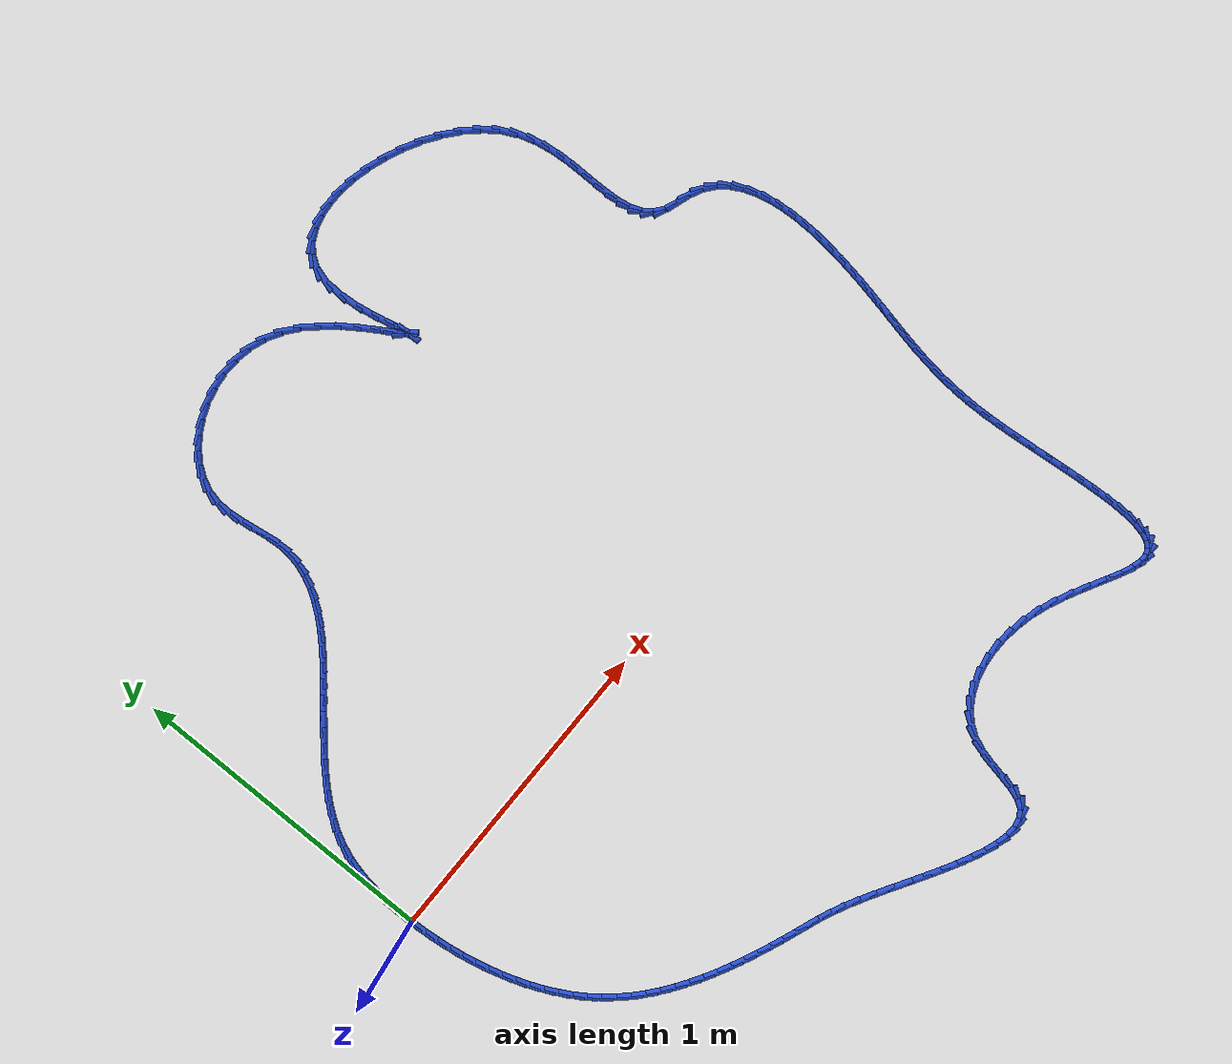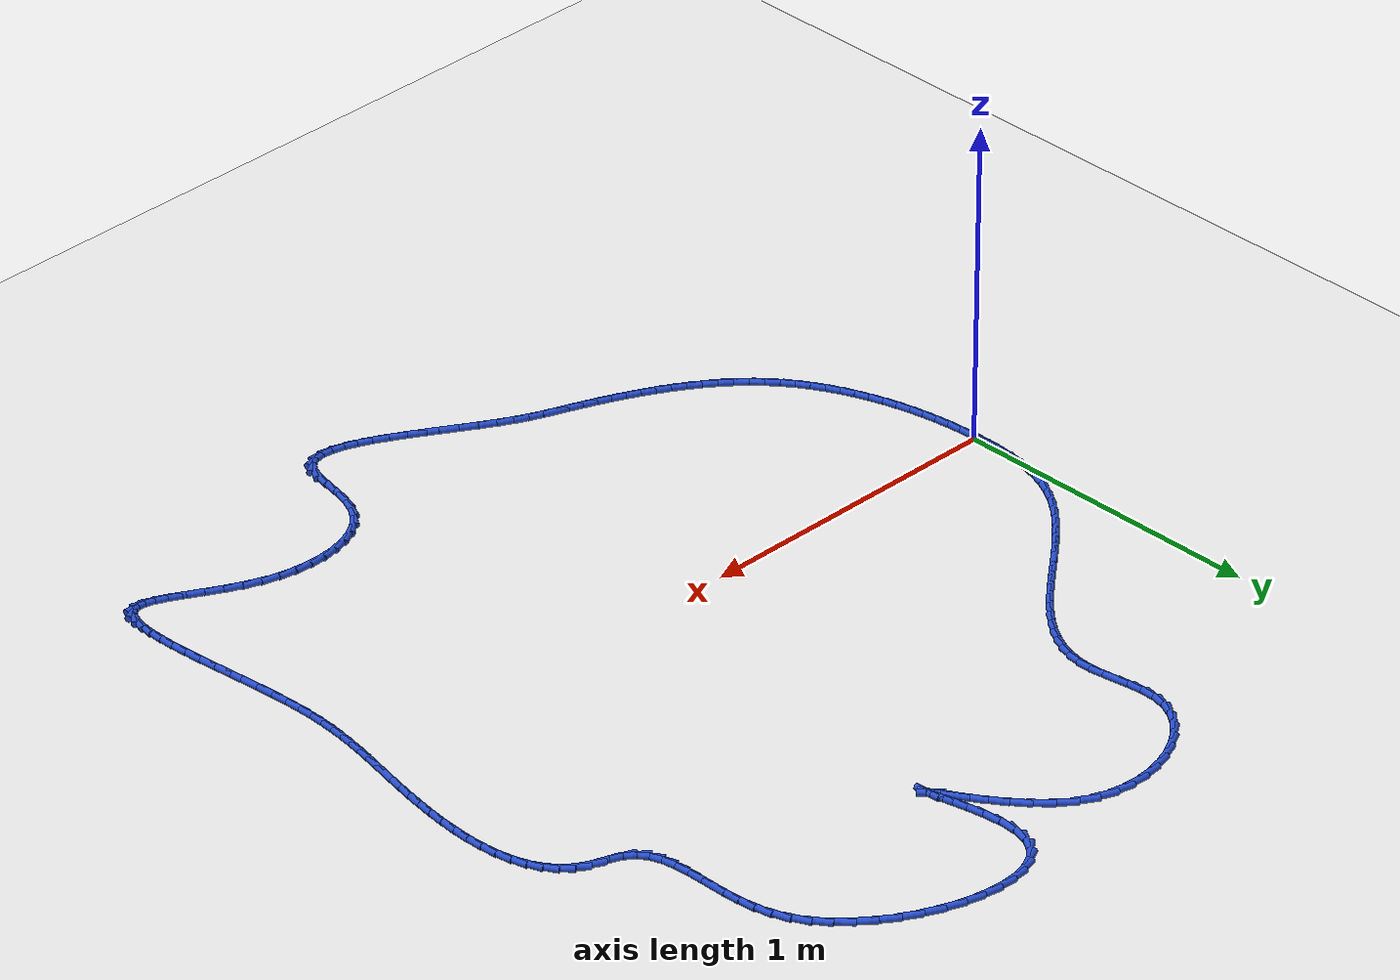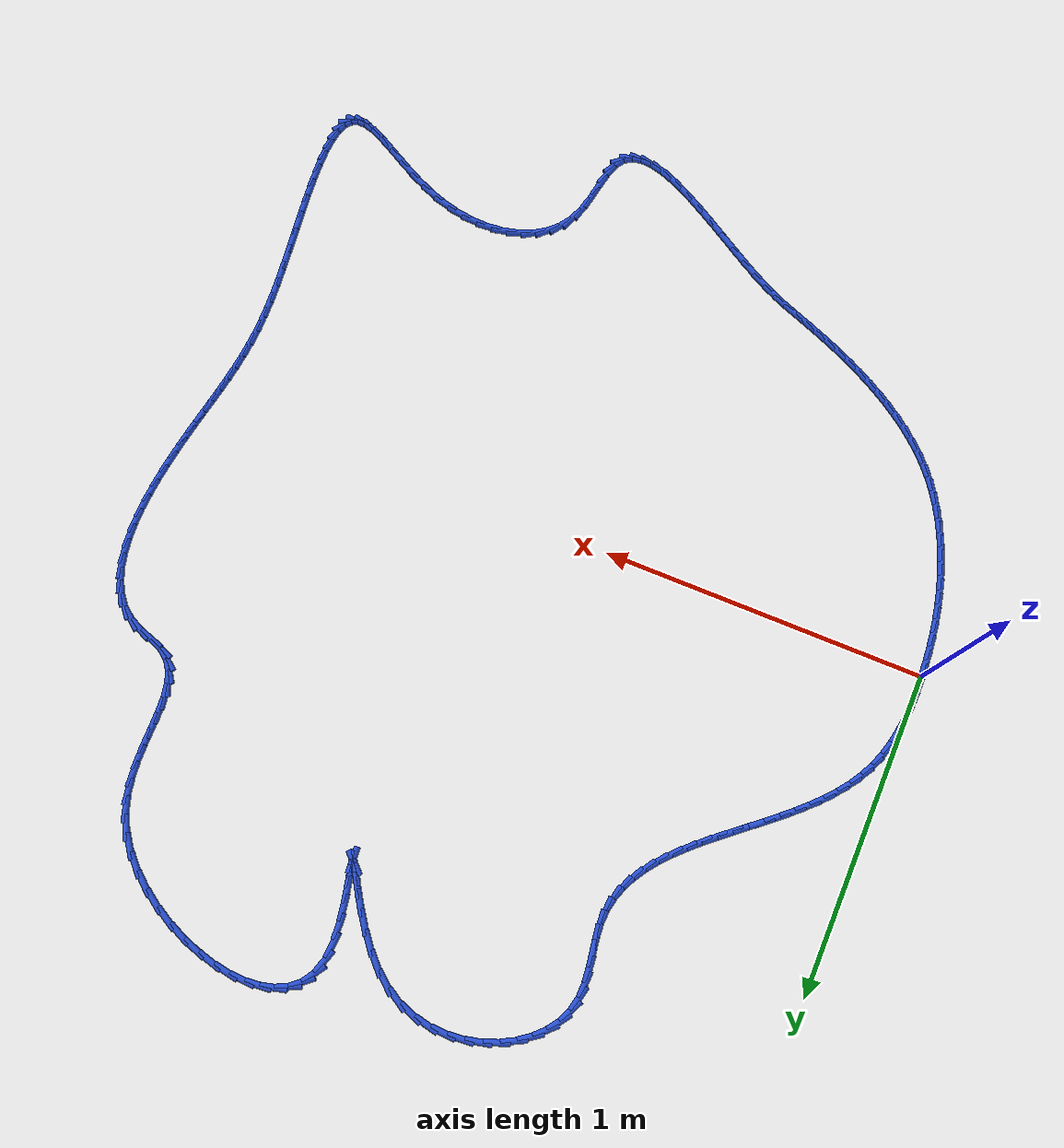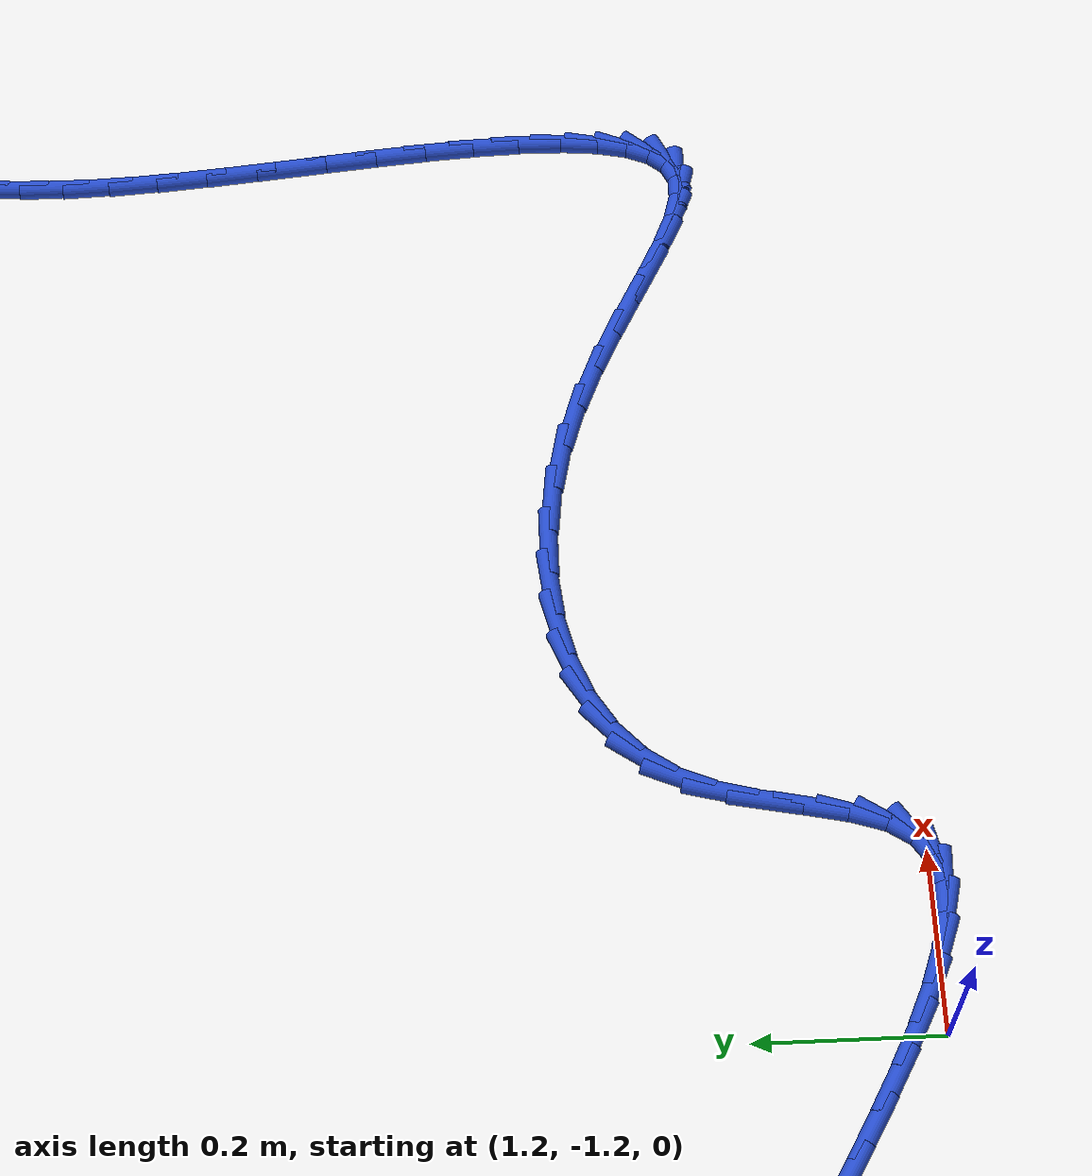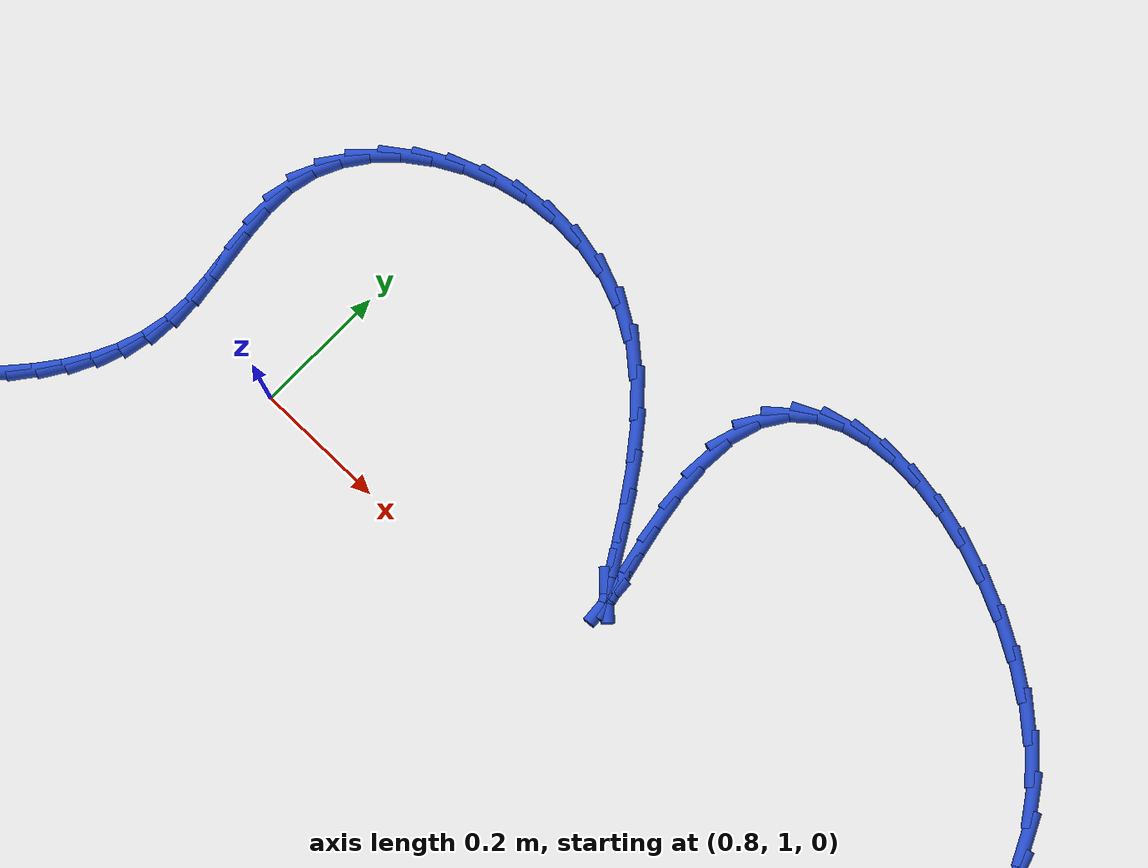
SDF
<sdf version="1.6">
 <world name="default">
  <light name="sun" type="directional">
   <pose>0 0 10 0 -0 0</pose>
   <diffuse>0.8 0.8 0.8 1</diffuse>
   <specular>0.2 0.2 0.2 1</specular>
   <attenuation>
    <range>1000</range>
    <constant>0.9</constant>
    <linear>0.01</linear>
    <quadratic>0.001</quadratic>
   </attenuation>
   <direction>-0.5 0.1 -0.9</direction>
  </light>
  <model name="ground_plane">
   <static>1</static>
   <link name="link">
    <collision name="collision">
     <geometry><plane><normal>0 0 1</normal><size>100 100</size></plane></geometry>
     <surface><friction><ode><mu>100</mu><mu2>50</mu2></ode></friction></surface>
    </collision>
    <visual name="visual">
     <cast_shadows>0</cast_shadows>
     <geometry><plane><normal>0 0 1</normal><size>100 100</size></plane></geometry>
     <material>
      <script><uri>file://media/materials/scripts/gazebo.material</uri><name>Gazebo/WhiteGlow</name></script>
     </material>
    </visual>
   </link>
  </model>
  <gravity>0 0 -9.8</gravity>
  <magnetic_field>6e-06 2.3e-05 -4.2e-05</magnetic_field>
  <atmosphere type="adiabatic"/>
  <physics name="default_physics" default="0" type="ode">
   <max_step_size>0.001</max_step_size>
   <real_time_factor>1</real_time_factor>
   <real_time_update_rate>1000</real_time_update_rate>
  </physics>
  <scene><ambient>0.4 0.4 0.4 1</ambient><background>0.7 0.7 0.7 1</background><shadows>1</shadows></scene>
  <spherical_coordinates>
   <surface_model>EARTH_WGS84</surface_model>
   <latitude_deg>0</latitude_deg>
   <longitude_deg>0</longitude_deg>
   <elevation>0</elevation>
   <heading_deg>0</heading_deg>
  </spherical_coordinates>
  <model name="line">
   <link name="link_0">
    <pose>-3.0357660829594124e-17 6.938893903907228e-18 0.01 0 1.57 -1.553074628439133</pose>
    <collision name="collision">
     <geometry><cylinder><radius>0.01</radius><length>0.08</length></cylinder></geometry>
    </collision>
    <visual name="visual">
     <material>
      <script><name>Gazebo/Blue</name><uri>file://media/materials/scripts/gazebo.material</uri></script>
     </material>
     <geometry><cylinder><radius>0.01</radius><length>0.08</length></cylinder></geometry>
    </visual>
   </link>
   <link name="link_1">
    <pose>-0.0007901279141245099 0.04458067060196605 0.01 0 1.57 1.549204396804768</pose>
    <collision name="collision">
     <geometry><cylinder><radius>0.01</radius><length>0.08</length></cylinder></geometry>
    </collision>
    <visual name="visual">
     <material>
      <script><name>Gazebo/Blue</name><uri>file://media/materials/scripts/gazebo.material</uri></script>
     </material>
     <geometry><cylinder><radius>0.01</radius><length>0.08</length></cylinder></geometry>
    </visual>
   </link>
   <link name="link_2">
    <pose>0.000174105443379259 0.0892308481333902 0.01 0 1.57 1.5001961556845738</pose>
    <collision name="collision">
     <geometry><cylinder><radius>0.01</radius><length>0.08</length></cylinder></geometry>
    </collision>
    <visual name="visual">
     <material>
      <script><name>Gazebo/Blue</name><uri>file://media/materials/scripts/gazebo.material</uri></script>
     </material>
     <geometry><cylinder><radius>0.01</radius><length>0.08</length></cylinder></geometry>
    </visual>
   </link>
   <link name="link_3">
    <pose>0.003315180171562166 0.13364793904845731 0.01 0 1.57 1.4407188430618099</pose>
    <collision name="collision">
     <geometry><cylinder><radius>0.01</radius><length>0.08</length></cylinder></geometry>
    </collision>
    <visual name="visual">
     <material>
      <script><name>Gazebo/Blue</name><uri>file://media/materials/scripts/gazebo.material</uri></script>
     </material>
     <geometry><cylinder><radius>0.01</radius><length>0.08</length></cylinder></geometry>
    </visual>
   </link>
   <link name="link_4">
    <pose>0.009055576369475104 0.17752934980135243 0.01 0 1.57 1.369972532111425</pose>
    <collision name="collision">
     <geometry><cylinder><radius>0.01</radius><length>0.08</length></cylinder></geometry>
    </collision>
    <visual name="visual">
     <material>
      <script><name>Gazebo/Blue</name><uri>file://media/materials/scripts/gazebo.material</uri></script>
     </material>
     <geometry><cylinder><radius>0.01</radius><length>0.08</length></cylinder></geometry>
    </visual>
   </link>
   <link name="link_5">
    <pose>0.01781777413616896 0.22057248684626019 0.01 0 1.57 1.2873325100912216</pose>
    <collision name="collision">
     <geometry><cylinder><radius>0.01</radius><length>0.08</length></cylinder></geometry>
    </collision>
    <visual name="visual">
     <material>
      <script><name>Gazebo/Blue</name><uri>file://media/materials/scripts/gazebo.material</uri></script>
     </material>
     <geometry><cylinder><radius>0.01</radius><length>0.08</length></cylinder></geometry>
    </visual>
   </link>
   <link name="link_6">
    <pose>0.03002425357069461 0.2624747566373655 0.01 0 1.57 1.1926419788531324</pose>
    <collision name="collision">
     <geometry><cylinder><radius>0.01</radius><length>0.08</length></cylinder></geometry>
    </collision>
    <visual name="visual">
     <material>
      <script><name>Gazebo/Blue</name><uri>file://media/materials/scripts/gazebo.material</uri></script>
     </material>
     <geometry><cylinder><radius>0.01</radius><length>0.08</length></cylinder></geometry>
    </visual>
   </link>
   <link name="link_7">
    <pose>0.04609749477210298 0.30293356562885343 0.01 0 1.57 1.0889990187016318</pose>
    <collision name="collision">
     <geometry><cylinder><radius>0.01</radius><length>0.08</length></cylinder></geometry>
    </collision>
    <visual name="visual">
     <material>
      <script><name>Gazebo/Blue</name><uri>file://media/materials/scripts/gazebo.material</uri></script>
     </material>
     <geometry><cylinder><radius>0.01</radius><length>0.08</length></cylinder></geometry>
    </visual>
   </link>
   <link name="link_8">
    <pose>0.06636599742501177 0.3416954748177271 0.01 0 1.57 0.9932835902297723</pose>
    <collision name="collision">
     <geometry><cylinder><radius>0.01</radius><length>0.08</length></cylinder></geometry>
    </collision>
    <visual name="visual">
     <material>
      <script><name>Gazebo/Blue</name><uri>file://media/materials/scripts/gazebo.material</uri></script>
     </material>
     <geometry><cylinder><radius>0.01</radius><length>0.08</length></cylinder></geometry>
    </visual>
   </link>
   <link name="link_9">
    <pose>0.09055778105871455 0.37882111412359 0.01 0 1.57 0.9121909174537467</pose>
    <collision name="collision">
     <geometry><cylinder><radius>0.01</radius><length>0.08</length></cylinder></geometry>
    </collision>
    <visual name="visual">
     <material>
      <script><name>Gazebo/Blue</name><uri>file://media/materials/scripts/gazebo.material</uri></script>
     </material>
     <geometry><cylinder><radius>0.01</radius><length>0.08</length></cylinder></geometry>
    </visual>
   </link>
   <link name="link_10">
    <pose>0.118164590096321 0.4144946923510066 0.01 0 1.57 0.8452936040650084</pose>
    <collision name="collision">
     <geometry><cylinder><radius>0.01</radius><length>0.08</length></cylinder></geometry>
    </collision>
    <visual name="visual">
     <material>
      <script><name>Gazebo/Blue</name><uri>file://media/materials/scripts/gazebo.material</uri></script>
     </material>
     <geometry><cylinder><radius>0.01</radius><length>0.08</length></cylinder></geometry>
    </visual>
   </link>
   <link name="link_11">
    <pose>0.14867760197149155 0.4489007148568321 0.01 0 1.57 0.7916272695713802</pose>
    <collision name="collision">
     <geometry><cylinder><radius>0.01</radius><length>0.08</length></cylinder></geometry>
    </collision>
    <visual name="visual">
     <material>
      <script><name>Gazebo/Blue</name><uri>file://media/materials/scripts/gazebo.material</uri></script>
     </material>
     <geometry><cylinder><radius>0.01</radius><length>0.08</length></cylinder></geometry>
    </visual>
   </link>
   <link name="link_12">
    <pose>0.1815879941178864 0.48222368699792134 0.01 0 1.57 0.750089971589212</pose>
    <collision name="collision">
     <geometry><cylinder><radius>0.01</radius><length>0.08</length></cylinder></geometry>
    </collision>
    <visual name="visual">
     <material>
      <script><name>Gazebo/Blue</name><uri>file://media/materials/scripts/gazebo.material</uri></script>
     </material>
     <geometry><cylinder><radius>0.01</radius><length>0.08</length></cylinder></geometry>
    </visual>
   </link>
   <link name="link_13">
    <pose>0.21638694396916622 0.5146481141311298 0.01 0 1.57 0.7196753319886483</pose>
    <collision name="collision">
     <geometry><cylinder><radius>0.01</radius><length>0.08</length></cylinder></geometry>
    </collision>
    <visual name="visual">
     <material>
      <script><name>Gazebo/Blue</name><uri>file://media/materials/scripts/gazebo.material</uri></script>
     </material>
     <geometry><cylinder><radius>0.01</radius><length>0.08</length></cylinder></geometry>
    </visual>
   </link>
   <link name="link_14">
    <pose>0.25256562895899115 0.5463585016133123 0.01 0 1.57 0.699595779834706</pose>
    <collision name="collision">
     <geometry><cylinder><radius>0.01</radius><length>0.08</length></cylinder></geometry>
    </collision>
    <visual name="visual">
     <material>
      <script><name>Gazebo/Blue</name><uri>file://media/materials/scripts/gazebo.material</uri></script>
     </material>
     <geometry><cylinder><radius>0.01</radius><length>0.08</length></cylinder></geometry>
    </visual>
   </link>
   <link name="link_15">
    <pose>0.2896152265210216 0.5775393548013241 0.01 0 1.57 0.6893415336585952</pose>
    <collision name="collision">
     <geometry><cylinder><radius>0.01</radius><length>0.08</length></cylinder></geometry>
    </collision>
    <visual name="visual">
     <material>
      <script><name>Gazebo/Blue</name><uri>file://media/materials/scripts/gazebo.material</uri></script>
     </material>
     <geometry><cylinder><radius>0.01</radius><length>0.08</length></cylinder></geometry>
    </visual>
   </link>
   <link name="link_16">
    <pose>0.32702691408891826 0.6083751790520205 0.01 0 1.57 0.6887087083756894</pose>
    <collision name="collision">
     <geometry><cylinder><radius>0.01</radius><length>0.08</length></cylinder></geometry>
    </collision>
    <visual name="visual">
     <material>
      <script><name>Gazebo/Blue</name><uri>file://media/materials/scripts/gazebo.material</uri></script>
     </material>
     <geometry><cylinder><radius>0.01</radius><length>0.08</length></cylinder></geometry>
    </visual>
   </link>
   <link name="link_17">
    <pose>0.36429186909634115 0.6390504797222563 0.01 0 1.57 0.6978166173289755</pose>
    <collision name="collision">
     <geometry><cylinder><radius>0.01</radius><length>0.08</length></cylinder></geometry>
    </collision>
    <visual name="visual">
     <material>
      <script><name>Gazebo/Blue</name><uri>file://media/materials/scripts/gazebo.material</uri></script>
     </material>
     <geometry><cylinder><radius>0.01</radius><length>0.08</length></cylinder></geometry>
    </visual>
   </link>
   <link name="link_18">
    <pose>0.4009012689769507 0.6697497621688865 0.01 0 1.57 0.7171237123761259</pose>
    <collision name="collision">
     <geometry><cylinder><radius>0.01</radius><length>0.08</length></cylinder></geometry>
    </collision>
    <visual name="visual">
     <material>
      <script><name>Gazebo/Blue</name><uri>file://media/materials/scripts/gazebo.material</uri></script>
     </material>
     <geometry><cylinder><radius>0.01</radius><length>0.08</length></cylinder></geometry>
    </visual>
   </link>
   <link name="link_19">
    <pose>0.43634629116440754 0.7006575317487665 0.01 0 1.57 0.7474424996967688</pose>
    <collision name="collision">
     <geometry><cylinder><radius>0.01</radius><length>0.08</length></cylinder></geometry>
    </collision>
    <visual name="visual">
     <material>
      <script><name>Gazebo/Blue</name><uri>file://media/materials/scripts/gazebo.material</uri></script>
     </material>
     <geometry><cylinder><radius>0.01</radius><length>0.08</length></cylinder></geometry>
    </visual>
   </link>
   <link name="link_20">
    <pose>0.4701181130923718 0.7319582938187513 0.01 0 1.57 0.789943108257413</pose>
    <collision name="collision">
     <geometry><cylinder><radius>0.01</radius><length>0.08</length></cylinder></geometry>
    </collision>
    <visual name="visual">
     <material>
      <script><name>Gazebo/Blue</name><uri>file://media/materials/scripts/gazebo.material</uri></script>
     </material>
     <geometry><cylinder><radius>0.01</radius><length>0.08</length></cylinder></geometry>
    </visual>
   </link>
   <link name="link_21">
    <pose>0.501707912194504 0.7638365537356961 0.01 0 1.57 0.8461189587645169</pose>
    <collision name="collision">
     <geometry><cylinder><radius>0.01</radius><length>0.08</length></cylinder></geometry>
    </collision>
    <visual name="visual">
     <material>
      <script><name>Gazebo/Blue</name><uri>file://media/materials/scripts/gazebo.material</uri></script>
     </material>
     <geometry><cylinder><radius>0.01</radius><length>0.08</length></cylinder></geometry>
    </visual>
   </link>
   <link name="link_22">
    <pose>0.5306068659044644 0.796476816856456 0.01 0 1.57 0.9176626161256145</pose>
    <collision name="collision">
     <geometry><cylinder><radius>0.01</radius><length>0.08</length></cylinder></geometry>
    </collision>
    <visual name="visual">
     <material>
      <script><name>Gazebo/Blue</name><uri>file://media/materials/scripts/gazebo.material</uri></script>
     </material>
     <geometry><cylinder><radius>0.01</radius><length>0.08</length></cylinder></geometry>
    </visual>
   </link>
   <link name="link_23">
    <pose>0.5563061516559136 0.8300635885378859 0.01 0 1.57 1.006168050811545</pose>
    <collision name="collision">
     <geometry><cylinder><radius>0.01</radius><length>0.08</length></cylinder></geometry>
    </collision>
    <visual name="visual">
     <material>
      <script><name>Gazebo/Blue</name><uri>file://media/materials/scripts/gazebo.material</uri></script>
     </material>
     <geometry><cylinder><radius>0.01</radius><length>0.08</length></cylinder></geometry>
    </visual>
   </link>
   <link name="link_24">
    <pose>0.5782969468825119 0.8647813741368411 0.01 0 1.57 1.1125620676882175</pose>
    <collision name="collision">
     <geometry><cylinder><radius>0.01</radius><length>0.08</length></cylinder></geometry>
    </collision>
    <visual name="visual">
     <material>
      <script><name>Gazebo/Blue</name><uri>file://media/materials/scripts/gazebo.material</uri></script>
     </material>
     <geometry><cylinder><radius>0.01</radius><length>0.08</length></cylinder></geometry>
    </visual>
   </link>
   <link name="link_25">
    <pose>0.5960704290179195 0.9008146790101768 0.01 0 1.57 1.2362430970811253</pose>
    <collision name="collision">
     <geometry><cylinder><radius>0.01</radius><length>0.08</length></cylinder></geometry>
    </collision>
    <visual name="visual">
     <material>
      <script><name>Gazebo/Blue</name><uri>file://media/materials/scripts/gazebo.material</uri></script>
     </material>
     <geometry><cylinder><radius>0.01</radius><length>0.08</length></cylinder></geometry>
    </visual>
   </link>
   <link name="link_26">
    <pose>0.609117775495797 0.9383480085147478 0.01 0 1.57 1.3741654403300576</pose>
    <collision name="collision">
     <geometry><cylinder><radius>0.01</radius><length>0.08</length></cylinder></geometry>
    </collision>
    <visual name="visual">
     <material>
      <script><name>Gazebo/Blue</name><uri>file://media/materials/scripts/gazebo.material</uri></script>
     </material>
     <geometry><cylinder><radius>0.01</radius><length>0.08</length></cylinder></geometry>
    </visual>
   </link>
   <link name="link_27">
    <pose>0.6169301637498048 0.9775658680074095 0.01 0 1.57 1.520465684541178</pose>
    <collision name="collision">
     <geometry><cylinder><radius>0.01</radius><length>0.08</length></cylinder></geometry>
    </collision>
    <visual name="visual">
     <material>
      <script><name>Gazebo/Blue</name><uri>file://media/materials/scripts/gazebo.material</uri></script>
     </material>
     <geometry><cylinder><radius>0.01</radius><length>0.08</length></cylinder></geometry>
    </visual>
   </link>
   <link name="link_28">
    <pose>0.6189998266631821 1.0186524689419427 0.01 0 1.57 -1.4917065667509501</pose>
    <collision name="collision">
     <geometry><cylinder><radius>0.01</radius><length>0.08</length></cylinder></geometry>
    </collision>
    <visual name="visual">
     <material>
      <script><name>Gazebo/Blue</name><uri>file://media/materials/scripts/gazebo.material</uri></script>
     </material>
     <geometry><cylinder><radius>0.01</radius><length>0.08</length></cylinder></geometry>
    </visual>
   </link>
   <link name="link_29">
    <pose>0.6155979898661069 1.0615751025445888 0.01 0 1.57 -1.425765584232859</pose>
    <collision name="collision">
     <geometry><cylinder><radius>0.01</radius><length>0.08</length></cylinder></geometry>
    </collision>
    <visual name="visual">
     <material>
      <script><name>Gazebo/Blue</name><uri>file://media/materials/scripts/gazebo.material</uri></script>
     </material>
     <geometry><cylinder><radius>0.01</radius><length>0.08</length></cylinder></geometry>
    </visual>
   </link>
   <link name="link_30">
    <pose>0.6091532271839346 1.1057003195812676 0.01 0 1.57 -1.4219051527942592</pose>
    <collision name="collision">
     <geometry><cylinder><radius>0.01</radius><length>0.08</length></cylinder></geometry>
    </collision>
    <visual name="visual">
     <material>
      <script><name>Gazebo/Blue</name><uri>file://media/materials/scripts/gazebo.material</uri></script>
     </material>
     <geometry><cylinder><radius>0.01</radius><length>0.08</length></cylinder></geometry>
    </visual>
   </link>
   <link name="link_31">
    <pose>0.6024644889751497 1.150291534861682 0.01 0 1.57 -1.477795868608527</pose>
    <collision name="collision">
     <geometry><cylinder><radius>0.01</radius><length>0.08</length></cylinder></geometry>
    </collision>
    <visual name="visual">
     <material>
      <script><name>Gazebo/Blue</name><uri>file://media/materials/scripts/gazebo.material</uri></script>
     </material>
     <geometry><cylinder><radius>0.01</radius><length>0.08</length></cylinder></geometry>
    </visual>
   </link>
   <link name="link_32">
    <pose>0.5983307255982356 1.1946121631955346 0.01 0 1.57 1.542633272863274</pose>
    <collision name="collision">
     <geometry><cylinder><radius>0.01</radius><length>0.08</length></cylinder></geometry>
    </collision>
    <visual name="visual">
     <material>
      <script><name>Gazebo/Blue</name><uri>file://media/materials/scripts/gazebo.material</uri></script>
     </material>
     <geometry><cylinder><radius>0.01</radius><length>0.08</length></cylinder></geometry>
    </visual>
   </link>
   <link name="link_33">
    <pose>0.599550887411677 1.2379256193925288 0.01 0 1.57 1.3505509018669752</pose>
    <collision name="collision">
     <geometry><cylinder><radius>0.01</radius><length>0.08</length></cylinder></geometry>
    </collision>
    <visual name="visual">
     <material>
      <script><name>Gazebo/Blue</name><uri>file://media/materials/scripts/gazebo.material</uri></script>
     </material>
     <geometry><cylinder><radius>0.01</radius><length>0.08</length></cylinder></geometry>
    </visual>
   </link>
   <link name="link_34">
    <pose>0.608857741209896 1.279496876197769 0.01 0 1.57 1.1322940176531735</pose>
    <collision name="collision">
     <geometry><cylinder><radius>0.01</radius><length>0.08</length></cylinder></geometry>
    </collision>
    <visual name="visual">
     <material>
      <script><name>Gazebo/Blue</name><uri>file://media/materials/scripts/gazebo.material</uri></script>
     </material>
     <geometry><cylinder><radius>0.01</radius><length>0.08</length></cylinder></geometry>
    </visual>
   </link>
   <link name="link_35">
    <pose>0.6272105496815719 1.318632653954447 0.01 0 1.57 0.9381526829207408</pose>
    <collision name="collision">
     <geometry><cylinder><radius>0.01</radius><length>0.08</length></cylinder></geometry>
    </collision>
    <visual name="visual">
     <material>
      <script><name>Gazebo/Blue</name><uri>file://media/materials/scripts/gazebo.material</uri></script>
     </material>
     <geometry><cylinder><radius>0.01</radius><length>0.08</length></cylinder></geometry>
    </visual>
   </link>
   <link name="link_36">
    <pose>0.6536431038155665 1.3546849978620055 0.01 0 1.57 0.7682769348026213</pose>
    <collision name="collision">
     <geometry><cylinder><radius>0.01</radius><length>0.08</length></cylinder></geometry>
    </collision>
    <visual name="visual">
     <material>
      <script><name>Gazebo/Blue</name><uri>file://media/materials/scripts/gazebo.material</uri></script>
     </material>
     <geometry><cylinder><radius>0.01</radius><length>0.08</length></cylinder></geometry>
    </visual>
   </link>
   <link name="link_37">
    <pose>0.6870925531043579 1.3870082280231897 0.01 0 1.57 0.616932547448426</pose>
    <collision name="collision">
     <geometry><cylinder><radius>0.01</radius><length>0.08</length></cylinder></geometry>
    </collision>
    <visual name="visual">
     <material>
      <script><name>Gazebo/Blue</name><uri>file://media/materials/scripts/gazebo.material</uri></script>
     </material>
     <geometry><cylinder><radius>0.01</radius><length>0.08</length></cylinder></geometry>
    </visual>
   </link>
   <link name="link_38">
    <pose>0.7264960470404243 1.4149566645407463 0.01 0 1.57 0.4776466507775044</pose>
    <collision name="collision">
     <geometry><cylinder><radius>0.01</radius><length>0.08</length></cylinder></geometry>
    </collision>
    <visual name="visual">
     <material>
      <script><name>Gazebo/Blue</name><uri>file://media/materials/scripts/gazebo.material</uri></script>
     </material>
     <geometry><cylinder><radius>0.01</radius><length>0.08</length></cylinder></geometry>
    </visual>
   </link>
   <link name="link_39">
    <pose>0.7707907351162429 1.4378846275174197 0.01 0 1.57 0.3444056914961959</pose>
    <collision name="collision">
     <geometry><cylinder><radius>0.01</radius><length>0.08</length></cylinder></geometry>
    </collision>
    <visual name="visual">
     <material>
      <script><name>Gazebo/Blue</name><uri>file://media/materials/scripts/gazebo.material</uri></script>
     </material>
     <geometry><cylinder><radius>0.01</radius><length>0.08</length></cylinder></geometry>
    </visual>
   </link>
   <link name="link_40">
    <pose>0.8189137668242923 1.4551464370559573 0.01 0 1.57 0.21194413332543177</pose>
    <collision name="collision">
     <geometry><cylinder><radius>0.01</radius><length>0.08</length></cylinder></geometry>
    </collision>
    <visual name="visual">
     <material>
      <script><name>Gazebo/Blue</name><uri>file://media/materials/scripts/gazebo.material</uri></script>
     </material>
     <geometry><cylinder><radius>0.01</radius><length>0.08</length></cylinder></geometry>
    </visual>
   </link>
   <link name="link_41">
    <pose>0.8698022916570498 1.4660964132591037 0.01 0 1.57 0.0757697522400697</pose>
    <collision name="collision">
     <geometry><cylinder><radius>0.01</radius><length>0.08</length></cylinder></geometry>
    </collision>
    <visual name="visual">
     <material>
      <script><name>Gazebo/Blue</name><uri>file://media/materials/scripts/gazebo.material</uri></script>
     </material>
     <geometry><cylinder><radius>0.01</radius><length>0.08</length></cylinder></geometry>
    </visual>
   </link>
   <link name="link_42">
    <pose>0.9223934591069932 1.4700888762296054 0.01 0 1.57 -0.06772764670613399</pose>
    <collision name="collision">
     <geometry><cylinder><radius>0.01</radius><length>0.08</length></cylinder></geometry>
    </collision>
    <visual name="visual">
     <material>
      <script><name>Gazebo/Blue</name><uri>file://media/materials/scripts/gazebo.material</uri></script>
     </material>
     <geometry><cylinder><radius>0.01</radius><length>0.08</length></cylinder></geometry>
    </visual>
   </link>
   <link name="link_43">
    <pose>0.9756244186666013 1.4664781460702083 0.01 0 1.57 -0.22091472987753152</pose>
    <collision name="collision">
     <geometry><cylinder><radius>0.01</radius><length>0.08</length></cylinder></geometry>
    </collision>
    <visual name="visual">
     <material>
      <script><name>Gazebo/Blue</name><uri>file://media/materials/scripts/gazebo.material</uri></script>
     </material>
     <geometry><cylinder><radius>0.01</radius><length>0.08</length></cylinder></geometry>
    </visual>
   </link>
   <link name="link_44">
    <pose>1.028432319828351 1.4546185428836576 0.01 0 1.57 -0.3842860537588678</pose>
    <collision name="collision">
     <geometry><cylinder><radius>0.01</radius><length>0.08</length></cylinder></geometry>
    </collision>
    <visual name="visual">
     <material>
      <script><name>Gazebo/Blue</name><uri>file://media/materials/scripts/gazebo.material</uri></script>
     </material>
     <geometry><cylinder><radius>0.01</radius><length>0.08</length></cylinder></geometry>
    </visual>
   </link>
   <link name="link_45">
    <pose>1.079754312084721 1.4338643867726997 0.01 0 1.57 -0.555788848875577</pose>
    <collision name="collision">
     <geometry><cylinder><radius>0.01</radius><length>0.08</length></cylinder></geometry>
    </collision>
    <visual name="visual">
     <material>
      <script><name>Gazebo/Blue</name><uri>file://media/materials/scripts/gazebo.material</uri></script>
     </material>
     <geometry><cylinder><radius>0.01</radius><length>0.08</length></cylinder></geometry>
    </visual>
   </link>
   <link name="link_46">
    <pose>1.1285277169356334 1.4035712963325608 0.01 0 1.57 -0.7169326110066782</pose>
    <collision name="collision">
     <geometry><cylinder><radius>0.01</radius><length>0.08</length></cylinder></geometry>
    </collision>
    <visual name="visual">
     <material>
      <script><name>Gazebo/Blue</name><uri>file://media/materials/scripts/gazebo.material</uri></script>
     </material>
     <geometry><cylinder><radius>0.01</radius><length>0.08</length></cylinder></geometry>
    </visual>
   </link>
   <link name="link_47">
    <pose>1.1738217427984357 1.3640905108471728 0.01 0 1.57 -0.8348408429273039</pose>
    <collision name="collision">
     <geometry><cylinder><radius>0.01</radius><length>0.08</length></cylinder></geometry>
    </collision>
    <visual name="visual">
     <material>
      <script><name>Gazebo/Blue</name><uri>file://media/materials/scripts/gazebo.material</uri></script>
     </material>
     <geometry><cylinder><radius>0.01</radius><length>0.08</length></cylinder></geometry>
    </visual>
   </link>
   <link name="link_48">
    <pose>1.2150727049811045 1.3185445771904358 0.01 0 1.57 -0.9180297185291241</pose>
    <collision name="collision">
     <geometry><cylinder><radius>0.01</radius><length>0.08</length></cylinder></geometry>
    </collision>
    <visual name="visual">
     <material>
      <script><name>Gazebo/Blue</name><uri>file://media/materials/scripts/gazebo.material</uri></script>
     </material>
     <geometry><cylinder><radius>0.01</radius><length>0.08</length></cylinder></geometry>
    </visual>
   </link>
   <link name="link_49">
    <pose>1.2517802848746813 1.2705343958477524 0.01 0 1.57 -0.9766913718913945</pose>
    <collision name="collision">
     <geometry><cylinder><radius>0.01</radius><length>0.08</length></cylinder></geometry>
    </collision>
    <visual name="visual">
     <material>
      <script><name>Gazebo/Blue</name><uri>file://media/materials/scripts/gazebo.material</uri></script>
     </material>
     <geometry><cylinder><radius>0.01</radius><length>0.08</length></cylinder></geometry>
    </visual>
   </link>
   <link name="link_50">
    <pose>1.2834441638702054 1.223660867304524 0.01 0 1.57 -1.0158768063774637</pose>
    <collision name="collision">
     <geometry><cylinder><radius>0.01</radius><length>0.08</length></cylinder></geometry>
    </collision>
    <visual name="visual">
     <material>
      <script><name>Gazebo/Blue</name><uri>file://media/materials/scripts/gazebo.material</uri></script>
     </material>
     <geometry><cylinder><radius>0.01</radius><length>0.08</length></cylinder></geometry>
    </visual>
   </link>
   <link name="link_51">
    <pose>1.3095640233587176 1.181524892046153 0.01 0 1.57 -1.034804785587061</pose>
    <collision name="collision">
     <geometry><cylinder><radius>0.01</radius><length>0.08</length></cylinder></geometry>
    </collision>
    <visual name="visual">
     <material>
      <script><name>Gazebo/Blue</name><uri>file://media/materials/scripts/gazebo.material</uri></script>
     </material>
     <geometry><cylinder><radius>0.01</radius><length>0.08</length></cylinder></geometry>
    </visual>
   </link>
   <link name="link_52">
    <pose>1.3296395447312575 1.1477273705580417 0.01 0 1.57 -1.0165014564160073</pose>
    <collision name="collision">
     <geometry><cylinder><radius>0.01</radius><length>0.08</length></cylinder></geometry>
    </collision>
    <visual name="visual">
     <material>
      <script><name>Gazebo/Blue</name><uri>file://media/materials/scripts/gazebo.material</uri></script>
     </material>
     <geometry><cylinder><radius>0.01</radius><length>0.08</length></cylinder></geometry>
    </visual>
   </link>
   <link name="link_53">
    <pose>1.3431704093788657 1.125869203325592 0.01 0 1.57 -0.7722796233946214</pose>
    <collision name="collision">
     <geometry><cylinder><radius>0.01</radius><length>0.08</length></cylinder></geometry>
    </collision>
    <visual name="visual">
     <material>
      <script><name>Gazebo/Blue</name><uri>file://media/materials/scripts/gazebo.material</uri></script>
     </material>
     <geometry><cylinder><radius>0.01</radius><length>0.08</length></cylinder></geometry>
    </visual>
   </link>
   <link name="link_54">
    <pose>1.3496562986925822 1.119551290834206 0.01 0 1.57 -1.5023184248114456</pose>
    <collision name="collision">
     <geometry><cylinder><radius>0.01</radius><length>0.08</length></cylinder></geometry>
    </collision>
    <visual name="visual">
     <material>
      <script><name>Gazebo/Blue</name><uri>file://media/materials/scripts/gazebo.material</uri></script>
     </material>
     <geometry><cylinder><radius>0.01</radius><length>0.08</length></cylinder></geometry>
    </visual>
   </link>
   <link name="link_55">
    <pose>1.348814385170932 1.131826741925614 0.01 0 1.57 -1.3494869806694105</pose>
    <collision name="collision">
     <geometry><cylinder><radius>0.01</radius><length>0.08</length></cylinder></geometry>
    </collision>
    <visual name="visual">
     <material>
      <script><name>Gazebo/Blue</name><uri>file://media/materials/scripts/gazebo.material</uri></script>
     </material>
     <geometry><cylinder><radius>0.01</radius><length>0.08</length></cylinder></geometry>
    </visual>
   </link>
   <link name="link_56">
    <pose>1.3422549294204558 1.1609805723535127 0.01 0 1.57 -1.3432836407676332</pose>
    <collision name="collision">
     <geometry><cylinder><radius>0.01</radius><length>0.08</length></cylinder></geometry>
    </collision>
    <visual name="visual">
     <material>
      <script><name>Gazebo/Blue</name><uri>file://media/materials/scripts/gazebo.material</uri></script>
     </material>
     <geometry><cylinder><radius>0.01</radius><length>0.08</length></cylinder></geometry>
    </visual>
   </link>
   <link name="link_57">
    <pose>1.3325629776388663 1.2028426197845807 0.01 0 1.57 -1.3704369343326024</pose>
    <collision name="collision">
     <geometry><cylinder><radius>0.01</radius><length>0.08</length></cylinder></geometry>
    </collision>
    <visual name="visual">
     <material>
      <script><name>Gazebo/Blue</name><uri>file://media/materials/scripts/gazebo.material</uri></script>
     </material>
     <geometry><cylinder><radius>0.01</radius><length>0.08</length></cylinder></geometry>
    </visual>
   </link>
   <link name="link_58">
    <pose>1.3223316334941435 1.2532224276540163 0.01 0 1.57 -1.422414729076723</pose>
    <collision name="collision">
     <geometry><cylinder><radius>0.01</radius><length>0.08</length></cylinder></geometry>
    </collision>
    <visual name="visual">
     <material>
      <script><name>Gazebo/Blue</name><uri>file://media/materials/scripts/gazebo.material</uri></script>
     </material>
     <geometry><cylinder><radius>0.01</radius><length>0.08</length></cylinder></geometry>
    </visual>
   </link>
   <link name="link_59">
    <pose>1.3141540006542662 1.30792953939702 0.01 0 1.57 -1.5065057109542699</pose>
    <collision name="collision">
     <geometry><cylinder><radius>0.01</radius><length>0.08</length></cylinder></geometry>
    </collision>
    <visual name="visual">
     <material>
      <script><name>Gazebo/Blue</name><uri>file://media/materials/scripts/gazebo.material</uri></script>
     </material>
     <geometry><cylinder><radius>0.01</radius><length>0.08</length></cylinder></geometry>
    </visual>
   </link>
   <link name="link_60">
    <pose>1.3106231827872132 1.3627734984487894 0.01 0 1.57 1.4978980653648977</pose>
    <collision name="collision">
     <geometry><cylinder><radius>0.01</radius><length>0.08</length></cylinder></geometry>
    </collision>
    <visual name="visual">
     <material>
      <script><name>Gazebo/Blue</name><uri>file://media/materials/scripts/gazebo.material</uri></script>
     </material>
     <geometry><cylinder><radius>0.01</radius><length>0.08</length></cylinder></geometry>
    </visual>
   </link>
   <link name="link_61">
    <pose>1.3143322835609634 1.4135638482445236 0.01 0 1.57 1.272125233787636</pose>
    <collision name="collision">
     <geometry><cylinder><radius>0.01</radius><length>0.08</length></cylinder></geometry>
    </collision>
    <visual name="visual">
     <material>
      <script><name>Gazebo/Blue</name><uri>file://media/materials/scripts/gazebo.material</uri></script>
     </material>
     <geometry><cylinder><radius>0.01</radius><length>0.08</length></cylinder></geometry>
    </visual>
   </link>
   <link name="link_62">
    <pose>1.3275524850675944 1.4565032015068826 0.01 0 1.57 0.9862299120974464</pose>
    <collision name="collision">
     <geometry><cylinder><radius>0.01</radius><length>0.08</length></cylinder></geometry>
    </collision>
    <visual name="visual">
     <material>
      <script><name>Gazebo/Blue</name><uri>file://media/materials/scripts/gazebo.material</uri></script>
     </material>
     <geometry><cylinder><radius>0.01</radius><length>0.08</length></cylinder></geometry>
    </visual>
   </link>
   <link name="link_63">
    <pose>1.3501783718741782 1.4906960190037257 0.01 0 1.57 0.697253401133908</pose>
    <collision name="collision">
     <geometry><cylinder><radius>0.01</radius><length>0.08</length></cylinder></geometry>
    </collision>
    <visual name="visual">
     <material>
      <script><name>Gazebo/Blue</name><uri>file://media/materials/scripts/gazebo.material</uri></script>
     </material>
     <geometry><cylinder><radius>0.01</radius><length>0.08</length></cylinder></geometry>
    </visual>
   </link>
   <link name="link_64">
    <pose>1.3810403486513816 1.5165461352166503 0.01 0 1.57 0.4413744814543036</pose>
    <collision name="collision">
     <geometry><cylinder><radius>0.01</radius><length>0.08</length></cylinder></geometry>
    </collision>
    <visual name="visual">
     <material>
      <script><name>Gazebo/Blue</name><uri>file://media/materials/scripts/gazebo.material</uri></script>
     </material>
     <geometry><cylinder><radius>0.01</radius><length>0.08</length></cylinder></geometry>
    </visual>
   </link>
   <link name="link_65">
    <pose>1.4189638221340357 1.5344634871541578 0.01 0 1.57 0.23295421601523145</pose>
    <collision name="collision">
     <geometry><cylinder><radius>0.01</radius><length>0.08</length></cylinder></geometry>
    </collision>
    <visual name="visual">
     <material>
      <script><name>Gazebo/Blue</name><uri>file://media/materials/scripts/gazebo.material</uri></script>
     </material>
     <geometry><cylinder><radius>0.01</radius><length>0.08</length></cylinder></geometry>
    </visual>
   </link>
   <link name="link_66">
    <pose>1.4627741990569696 1.544858011824748 0.01 0 1.57 0.06752809785762076</pose>
    <collision name="collision">
     <geometry><cylinder><radius>0.01</radius><length>0.08</length></cylinder></geometry>
    </collision>
    <visual name="visual">
     <material>
      <script><name>Gazebo/Blue</name><uri>file://media/materials/scripts/gazebo.material</uri></script>
     </material>
     <geometry><cylinder><radius>0.01</radius><length>0.08</length></cylinder></geometry>
    </visual>
   </link>
   <link name="link_67">
    <pose>1.5112968861550142 1.5481396462369226 0.01 0 1.57 -0.06562388815619034</pose>
    <collision name="collision">
     <geometry><cylinder><radius>0.01</radius><length>0.08</length></cylinder></geometry>
    </collision>
    <visual name="visual">
     <material>
      <script><name>Gazebo/Blue</name><uri>file://media/materials/scripts/gazebo.material</uri></script>
     </material>
     <geometry><cylinder><radius>0.01</radius><length>0.08</length></cylinder></geometry>
    </visual>
   </link>
   <link name="link_68">
    <pose>1.5633572901629997 1.5447183273991827 0.01 0 1.57 -0.17663492208632015</pose>
    <collision name="collision">
     <geometry><cylinder><radius>0.01</radius><length>0.08</length></cylinder></geometry>
    </collision>
    <visual name="visual">
     <material>
      <script><name>Gazebo/Blue</name><uri>file://media/materials/scripts/gazebo.material</uri></script>
     </material>
     <geometry><cylinder><radius>0.01</radius><length>0.08</length></cylinder></geometry>
    </visual>
   </link>
   <link name="link_69">
    <pose>1.6177808178157567 1.5350039923200287 0.01 0 1.57 -0.2734428203003848</pose>
    <collision name="collision">
     <geometry><cylinder><radius>0.01</radius><length>0.08</length></cylinder></geometry>
    </collision>
    <visual name="visual">
     <material>
      <script><name>Gazebo/Blue</name><uri>file://media/materials/scripts/gazebo.material</uri></script>
     </material>
     <geometry><cylinder><radius>0.01</radius><length>0.08</length></cylinder></geometry>
    </visual>
   </link>
   <link name="link_70">
    <pose>1.6733928758481142 1.5194065780079615 0.01 0 1.57 -0.3620890400443482</pose>
    <collision name="collision">
     <geometry><cylinder><radius>0.01</radius><length>0.08</length></cylinder></geometry>
    </collision>
    <visual name="visual">
     <material>
      <script><name>Gazebo/Blue</name><uri>file://media/materials/scripts/gazebo.material</uri></script>
     </material>
     <geometry><cylinder><radius>0.01</radius><length>0.08</length></cylinder></geometry>
    </visual>
   </link>
   <link name="link_71">
    <pose>1.7290188709949041 1.4983360214714831 0.01 0 1.57 -0.4473766975733315</pose>
    <collision name="collision">
     <geometry><cylinder><radius>0.01</radius><length>0.08</length></cylinder></geometry>
    </collision>
    <visual name="visual">
     <material>
      <script><name>Gazebo/Blue</name><uri>file://media/materials/scripts/gazebo.material</uri></script>
     </material>
     <geometry><cylinder><radius>0.01</radius><length>0.08</length></cylinder></geometry>
    </visual>
   </link>
   <link name="link_72">
    <pose>1.7834842099909567 1.4722022597190934 0.01 0 1.57 -0.5334648285504336</pose>
    <collision name="collision">
     <geometry><cylinder><radius>0.01</radius><length>0.08</length></cylinder></geometry>
    </collision>
    <visual name="visual">
     <material>
      <script><name>Gazebo/Blue</name><uri>file://media/materials/scripts/gazebo.material</uri></script>
     </material>
     <geometry><cylinder><radius>0.01</radius><length>0.08</length></cylinder></geometry>
    </visual>
   </link>
   <link name="link_73">
    <pose>1.8356142995711016 1.4414152297592935 0.01 0 1.57 -0.6243451373747428</pose>
    <collision name="collision">
     <geometry><cylinder><radius>0.01</radius><length>0.08</length></cylinder></geometry>
    </collision>
    <visual name="visual">
     <material>
      <script><name>Gazebo/Blue</name><uri>file://media/materials/scripts/gazebo.material</uri></script>
     </material>
     <geometry><cylinder><radius>0.01</radius><length>0.08</length></cylinder></geometry>
    </visual>
   </link>
   <link name="link_74">
    <pose>1.8842345464701693 1.4063848686005846 0.01 0 1.57 -0.7242175810839562</pose>
    <collision name="collision">
     <geometry><cylinder><radius>0.01</radius><length>0.08</length></cylinder></geometry>
    </collision>
    <visual name="visual">
     <material>
      <script><name>Gazebo/Blue</name><uri>file://media/materials/scripts/gazebo.material</uri></script>
     </material>
     <geometry><cylinder><radius>0.01</radius><length>0.08</length></cylinder></geometry>
    </visual>
   </link>
   <link name="link_75">
    <pose>1.92817035742299 1.3675211132514675 0.01 0 1.57 -0.8377423098663479</pose>
    <collision name="collision">
     <geometry><cylinder><radius>0.01</radius><length>0.08</length></cylinder></geometry>
    </collision>
    <visual name="visual">
     <material>
      <script><name>Gazebo/Blue</name><uri>file://media/materials/scripts/gazebo.material</uri></script>
     </material>
     <geometry><cylinder><radius>0.01</radius><length>0.08</length></cylinder></geometry>
    </visual>
   </link>
   <link name="link_76">
    <pose>1.9662471391643948 1.3252339007204432 0.01 0 1.57 -0.9700259372270136</pose>
    <collision name="collision">
     <geometry><cylinder><radius>0.01</radius><length>0.08</length></cylinder></geometry>
    </collision>
    <visual name="visual">
     <material>
      <script><name>Gazebo/Blue</name><uri>file://media/materials/scripts/gazebo.material</uri></script>
     </material>
     <geometry><cylinder><radius>0.01</radius><length>0.08</length></cylinder></geometry>
    </visual>
   </link>
   <link name="link_77">
    <pose>1.9972902984292134 1.2799331680160129 0.01 0 1.57 -1.1251586003778402</pose>
    <collision name="collision">
     <geometry><cylinder><radius>0.01</radius><length>0.08</length></cylinder></geometry>
    </collision>
    <visual name="visual">
     <material>
      <script><name>Gazebo/Blue</name><uri>file://media/materials/scripts/gazebo.material</uri></script>
     </material>
     <geometry><cylinder><radius>0.01</radius><length>0.08</length></cylinder></geometry>
    </visual>
   </link>
   <link name="link_78">
    <pose>2.0201701926653914 1.2320358334792347 0.01 0 1.57 -1.2806554762151443</pose>
    <collision name="collision">
     <geometry><cylinder><radius>0.01</radius><length>0.08</length></cylinder></geometry>
    </collision>
    <visual name="visual">
     <material>
      <script><name>Gazebo/Blue</name><uri>file://media/materials/scripts/gazebo.material</uri></script>
     </material>
     <geometry><cylinder><radius>0.01</radius><length>0.08</length></cylinder></geometry>
    </visual>
   </link>
   <link name="link_79">
    <pose>2.035061036378018 1.1821613185727535 0.01 0 1.57 -1.4046998382544418</pose>
    <collision name="collision">
     <geometry><cylinder><radius>0.01</radius><length>0.08</length></cylinder></geometry>
    </collision>
    <visual name="visual">
     <material>
      <script><name>Gazebo/Blue</name><uri>file://media/materials/scripts/gazebo.material</uri></script>
     </material>
     <geometry><cylinder><radius>0.01</radius><length>0.08</length></cylinder></geometry>
    </visual>
   </link>
   <link name="link_80">
    <pose>2.04361128006563 1.131158009574793 0.01 0 1.57 -1.4941538290474041</pose>
    <collision name="collision">
     <geometry><cylinder><radius>0.01</radius><length>0.08</length></cylinder></geometry>
    </collision>
    <visual name="visual">
     <material>
      <script><name>Gazebo/Blue</name><uri>file://media/materials/scripts/gazebo.material</uri></script>
     </material>
     <geometry><cylinder><radius>0.01</radius><length>0.08</length></cylinder></geometry>
    </visual>
   </link>
   <link name="link_81">
    <pose>2.047548561925842 1.079886591470835 0.01 0 1.57 -1.5500419618869712</pose>
    <collision name="collision">
     <geometry><cylinder><radius>0.01</radius><length>0.08</length></cylinder></geometry>
    </collision>
    <visual name="visual">
     <material>
      <script><name>Gazebo/Blue</name><uri>file://media/materials/scripts/gazebo.material</uri></script>
     </material>
     <geometry><cylinder><radius>0.01</radius><length>0.08</length></cylinder></geometry>
    </visual>
   </link>
   <link name="link_82">
    <pose>2.0486005201562643 1.0292077492463625 0.01 0 1.57 1.5686485199787221</pose>
    <collision name="collision">
     <geometry><cylinder><radius>0.01</radius><length>0.08</length></cylinder></geometry>
    </collision>
    <visual name="visual">
     <material>
      <script><name>Gazebo/Blue</name><uri>file://media/materials/scripts/gazebo.material</uri></script>
     </material>
     <geometry><cylinder><radius>0.01</radius><length>0.08</length></cylinder></geometry>
    </visual>
   </link>
   <link name="link_83">
    <pose>2.0484947929545143 0.9799821678868582 0.01 0 1.57 -1.5609009051936824</pose>
    <collision name="collision">
     <geometry><cylinder><radius>0.01</radius><length>0.08</length></cylinder></geometry>
    </collision>
    <visual name="visual">
     <material>
      <script><name>Gazebo/Blue</name><uri>file://media/materials/scripts/gazebo.material</uri></script>
     </material>
     <geometry><cylinder><radius>0.01</radius><length>0.08</length></cylinder></geometry>
    </visual>
   </link>
   <link name="link_84">
    <pose>2.0489590185182025 0.9330705323778046 0.01 0 1.57 -1.5077340648190145</pose>
    <collision name="collision">
     <geometry><cylinder><radius>0.01</radius><length>0.08</length></cylinder></geometry>
    </collision>
    <visual name="visual">
     <material>
      <script><name>Gazebo/Blue</name><uri>file://media/materials/scripts/gazebo.material</uri></script>
     </material>
     <geometry><cylinder><radius>0.01</radius><length>0.08</length></cylinder></geometry>
    </visual>
   </link>
   <link name="link_85">
    <pose>2.0517208350449443 0.8893335277046835 0.01 0 1.57 -1.401481971332941</pose>
    <collision name="collision">
     <geometry><cylinder><radius>0.01</radius><length>0.08</length></cylinder></geometry>
    </collision>
    <visual name="visual">
     <material>
      <script><name>Gazebo/Blue</name><uri>file://media/materials/scripts/gazebo.material</uri></script>
     </material>
     <geometry><cylinder><radius>0.01</radius><length>0.08</length></cylinder></geometry>
    </visual>
   </link>
   <link name="link_86">
    <pose>2.0585078807323525 0.8496318388529785 0.01 0 1.57 -1.2249898475581995</pose>
    <collision name="collision">
     <geometry><cylinder><radius>0.01</radius><length>0.08</length></cylinder></geometry>
    </collision>
    <visual name="visual">
     <material>
      <script><name>Gazebo/Blue</name><uri>file://media/materials/scripts/gazebo.material</uri></script>
     </material>
     <geometry><cylinder><radius>0.01</radius><length>0.08</length></cylinder></geometry>
    </visual>
   </link>
   <link name="link_87">
    <pose>2.0710477937780403 0.8148261508081717 0.01 0 1.57 -0.9673591083011305</pose>
    <collision name="collision">
     <geometry><cylinder><radius>0.01</radius><length>0.08</length></cylinder></geometry>
    </collision>
    <visual name="visual">
     <material>
      <script><name>Gazebo/Blue</name><uri>file://media/materials/scripts/gazebo.material</uri></script>
     </material>
     <geometry><cylinder><radius>0.01</radius><length>0.08</length></cylinder></geometry>
    </visual>
   </link>
   <link name="link_88">
    <pose>2.09106821237962 0.7857771485557453 0.01 0 1.57 -0.6545795780663911</pose>
    <collision name="collision">
     <geometry><cylinder><radius>0.01</radius><length>0.08</length></cylinder></geometry>
    </collision>
    <visual name="visual">
     <material>
      <script><name>Gazebo/Blue</name><uri>file://media/materials/scripts/gazebo.material</uri></script>
     </material>
     <geometry><cylinder><radius>0.01</radius><length>0.08</length></cylinder></geometry>
    </visual>
   </link>
   <link name="link_89">
    <pose>2.1202967747347072 0.7633455170811826 0.01 0 1.57 -0.3870024964024734</pose>
    <collision name="collision">
     <geometry><cylinder><radius>0.01</radius><length>0.08</length></cylinder></geometry>
    </collision>
    <visual name="visual">
     <material>
      <script><name>Gazebo/Blue</name><uri>file://media/materials/scripts/gazebo.material</uri></script>
     </material>
     <geometry><cylinder><radius>0.01</radius><length>0.08</length></cylinder></geometry>
    </visual>
   </link>
   <link name="link_90">
    <pose>2.1592436663225203 0.7474725074676193 0.01 0 1.57 -0.3262584201818298</pose>
    <collision name="collision">
     <geometry><cylinder><radius>0.01</radius><length>0.08</length></cylinder></geometry>
    </collision>
    <visual name="visual">
     <material>
      <script><name>Gazebo/Blue</name><uri>file://media/materials/scripts/gazebo.material</uri></script>
     </material>
     <geometry><cylinder><radius>0.01</radius><length>0.08</length></cylinder></geometry>
    </visual>
   </link>
   <link name="link_91">
    <pose>2.201775322750322 0.7330819366270795 0.01 0 1.57 -0.46458634883396543</pose>
    <collision name="collision">
     <geometry><cylinder><radius>0.01</radius><length>0.08</length></cylinder></geometry>
    </collision>
    <visual name="visual">
     <material>
      <script><name>Gazebo/Blue</name><uri>file://media/materials/scripts/gazebo.material</uri></script>
     </material>
     <geometry><cylinder><radius>0.01</radius><length>0.08</length></cylinder></geometry>
    </visual>
   </link>
   <link name="link_92">
    <pose>2.240081813916022 0.7138837201366212 0.01 0 1.57 -0.6830885526209128</pose>
    <collision name="collision">
     <geometry><cylinder><radius>0.01</radius><length>0.08</length></cylinder></geometry>
    </collision>
    <visual name="visual">
     <material>
      <script><name>Gazebo/Blue</name><uri>file://media/materials/scripts/gazebo.material</uri></script>
     </material>
     <geometry><cylinder><radius>0.01</radius><length>0.08</length></cylinder></geometry>
    </visual>
   </link>
   <link name="link_93">
    <pose>2.271727751603935 0.6881308116999021 0.01 0 1.57 -0.8922184669051937</pose>
    <collision name="collision">
     <geometry><cylinder><radius>0.01</radius><length>0.08</length></cylinder></geometry>
    </collision>
    <visual name="visual">
     <material>
      <script><name>Gazebo/Blue</name><uri>file://media/materials/scripts/gazebo.material</uri></script>
     </material>
     <geometry><cylinder><radius>0.01</radius><length>0.08</length></cylinder></geometry>
    </visual>
   </link>
   <link name="link_94">
    <pose>2.297196898308863 0.6565435994764391 0.01 0 1.57 -1.0756680846532445</pose>
    <collision name="collision">
     <geometry><cylinder><radius>0.01</radius><length>0.08</length></cylinder></geometry>
    </collision>
    <visual name="visual">
     <material>
      <script><name>Gazebo/Blue</name><uri>file://media/materials/scripts/gazebo.material</uri></script>
     </material>
     <geometry><cylinder><radius>0.01</radius><length>0.08</length></cylinder></geometry>
    </visual>
   </link>
   <link name="link_95">
    <pose>2.3170020276628724 0.6198669935113165 0.01 0 1.57 -1.2276967945687367</pose>
    <collision name="collision">
     <geometry><cylinder><radius>0.01</radius><length>0.08</length></cylinder></geometry>
    </collision>
    <visual name="visual">
     <material>
      <script><name>Gazebo/Blue</name><uri>file://media/materials/scripts/gazebo.material</uri></script>
     </material>
     <geometry><cylinder><radius>0.01</radius><length>0.08</length></cylinder></geometry>
    </visual>
   </link>
   <link name="link_96">
    <pose>2.3316559132980266 0.5788459038496178 0.01 0 1.57 -1.3499988795147575</pose>
    <collision name="collision">
     <geometry><cylinder><radius>0.01</radius><length>0.08</length></cylinder></geometry>
    </collision>
    <visual name="visual">
     <material>
      <script><name>Gazebo/Blue</name><uri>file://media/materials/scripts/gazebo.material</uri></script>
     </material>
     <geometry><cylinder><radius>0.01</radius><length>0.08</length></cylinder></geometry>
    </visual>
   </link>
   <link name="link_97">
    <pose>2.3416713288463886 0.5342252405364257 0.01 0 1.57 -1.4473684288900597</pose>
    <collision name="collision">
     <geometry><cylinder><radius>0.01</radius><length>0.08</length></cylinder></geometry>
    </collision>
    <visual name="visual">
     <material>
      <script><name>Gazebo/Blue</name><uri>file://media/materials/scripts/gazebo.material</uri></script>
     </material>
     <geometry><cylinder><radius>0.01</radius><length>0.08</length></cylinder></geometry>
    </visual>
   </link>
   <link name="link_98">
    <pose>2.3475610479400224 0.48674991361682446 0.01 0 1.57 -1.5249115936790276</pose>
    <collision name="collision">
     <geometry><cylinder><radius>0.01</radius><length>0.08</length></cylinder></geometry>
    </collision>
    <visual name="visual">
     <material>
      <script><name>Gazebo/Blue</name><uri>file://media/materials/scripts/gazebo.material</uri></script>
     </material>
     <geometry><cylinder><radius>0.01</radius><length>0.08</length></cylinder></geometry>
    </visual>
   </link>
   <link name="link_99">
    <pose>2.3498378442109913 0.4371648331358975 0.01 0 1.57 1.5546376911339679</pose>
    <collision name="collision">
     <geometry><cylinder><radius>0.01</radius><length>0.08</length></cylinder></geometry>
    </collision>
    <visual name="visual">
     <material>
      <script><name>Gazebo/Blue</name><uri>file://media/materials/scripts/gazebo.material</uri></script>
     </material>
     <geometry><cylinder><radius>0.01</radius><length>0.08</length></cylinder></geometry>
    </visual>
   </link>
   <link name="link_100">
    <pose>2.349014491291359 0.3862149091387283 0.01 0 1.57 1.5047544848372976</pose>
    <collision name="collision">
     <geometry><cylinder><radius>0.01</radius><length>0.08</length></cylinder></geometry>
    </collision>
    <visual name="visual">
     <material>
      <script><name>Gazebo/Blue</name><uri>file://media/materials/scripts/gazebo.material</uri></script>
     </material>
     <geometry><cylinder><radius>0.01</radius><length>0.08</length></cylinder></geometry>
    </visual>
   </link>
   <link name="link_101">
    <pose>2.3456037628131905 0.33464505167040065 0.01 0 1.57 1.4645722780135277</pose>
    <collision name="collision">
     <geometry><cylinder><radius>0.01</radius><length>0.08</length></cylinder></geometry>
    </collision>
    <visual name="visual">
     <material>
      <script><name>Gazebo/Blue</name><uri>file://media/materials/scripts/gazebo.material</uri></script>
     </material>
     <geometry><cylinder><radius>0.01</radius><length>0.08</length></cylinder></geometry>
    </visual>
   </link>
   <link name="link_102">
    <pose>2.3401184324085484 0.283200170775998 0.01 0 1.57 1.4323470001797607</pose>
    <collision name="collision">
     <geometry><cylinder><radius>0.01</radius><length>0.08</length></cylinder></geometry>
    </collision>
    <visual name="visual">
     <material>
      <script><name>Gazebo/Blue</name><uri>file://media/materials/scripts/gazebo.material</uri></script>
     </material>
     <geometry><cylinder><radius>0.01</radius><length>0.08</length></cylinder></geometry>
    </visual>
   </link>
   <link name="link_103">
    <pose>2.3330712737094954 0.23262517650060388 0.01 0 1.57 1.406916186241533</pose>
    <collision name="collision">
     <geometry><cylinder><radius>0.01</radius><length>0.08</length></cylinder></geometry>
    </collision>
    <visual name="visual">
     <material>
      <script><name>Gazebo/Blue</name><uri>file://media/materials/scripts/gazebo.material</uri></script>
     </material>
     <geometry><cylinder><radius>0.01</radius><length>0.08</length></cylinder></geometry>
    </visual>
   </link>
   <link name="link_104">
    <pose>2.3249750603480965 0.18366497888930194 0.01 0 1.57 1.3875560495807224</pose>
    <collision name="collision">
     <geometry><cylinder><radius>0.01</radius><length>0.08</length></cylinder></geometry>
    </collision>
    <visual name="visual">
     <material>
      <script><name>Gazebo/Blue</name><uri>file://media/materials/scripts/gazebo.material</uri></script>
     </material>
     <geometry><cylinder><radius>0.01</radius><length>0.08</length></cylinder></geometry>
    </visual>
   </link>
   <link name="link_105">
    <pose>2.316328544336196 0.13700752926711304 0.01 0 1.57 1.3734585838072135</pose>
    <collision name="collision">
     <geometry><cylinder><radius>0.01</radius><length>0.08</length></cylinder></geometry>
    </collision>
    <visual name="visual">
     <material>
      <script><name>Gazebo/Blue</name><uri>file://media/materials/scripts/gazebo.material</uri></script>
     </material>
     <geometry><cylinder><radius>0.01</radius><length>0.08</length></cylinder></geometry>
    </visual>
   </link>
   <link name="link_106">
    <pose>2.307456583787551 0.09263438599540294 0.01 0 1.57 1.3649897628562466</pose>
    <collision name="collision">
     <geometry><cylinder><radius>0.01</radius><length>0.08</length></cylinder></geometry>
    </collision>
    <visual name="visual">
     <material>
      <script><name>Gazebo/Blue</name><uri>file://media/materials/scripts/gazebo.material</uri></script>
     </material>
     <geometry><cylinder><radius>0.01</radius><length>0.08</length></cylinder></geometry>
    </visual>
   </link>
   <link name="link_107">
    <pose>2.2985664485890385 0.050049439748573704 0.01 0 1.57 1.3631116732076547</pose>
    <collision name="collision">
     <geometry><cylinder><radius>0.01</radius><length>0.08</length></cylinder></geometry>
    </collision>
    <visual name="visual">
     <material>
      <script><name>Gazebo/Blue</name><uri>file://media/materials/scripts/gazebo.material</uri></script>
     </material>
     <geometry><cylinder><radius>0.01</radius><length>0.08</length></cylinder></geometry>
    </visual>
   </link>
   <link name="link_108">
    <pose>2.2898631913520653 0.00874757416968108 0.01 0 1.57 1.3685047364045335</pose>
    <collision name="collision">
     <geometry><cylinder><radius>0.01</radius><length>0.08</length></cylinder></geometry>
    </collision>
    <visual name="visual">
     <material>
      <script><name>Gazebo/Blue</name><uri>file://media/materials/scripts/gazebo.material</uri></script>
     </material>
     <geometry><cylinder><radius>0.01</radius><length>0.08</length></cylinder></geometry>
    </visual>
   </link>
   <link name="link_109">
    <pose>2.281551864688037 -0.03177632709821929 0.01 0 1.57 1.3814368625527615</pose>
    <collision name="collision">
     <geometry><cylinder><radius>0.01</radius><length>0.08</length></cylinder></geometry>
    </collision>
    <visual name="visual">
     <material>
      <script><name>Gazebo/Blue</name><uri>file://media/materials/scripts/gazebo.material</uri></script>
     </material>
     <geometry><cylinder><radius>0.01</radius><length>0.08</length></cylinder></geometry>
    </visual>
   </link>
   <link name="link_110">
    <pose>2.2738375212083612 -0.07202738041207159 0.01 0 1.57 1.401682594650171</pose>
    <collision name="collision">
     <geometry><cylinder><radius>0.01</radius><length>0.08</length></cylinder></geometry>
    </collision>
    <visual name="visual">
     <material>
      <script><name>Gazebo/Blue</name><uri>file://media/materials/scripts/gazebo.material</uri></script>
     </material>
     <geometry><cylinder><radius>0.01</radius><length>0.08</length></cylinder></geometry>
    </visual>
   </link>
   <link name="link_111">
    <pose>2.2669252135244435 -0.11251070212882018 0.01 0 1.57 1.4285059001752896</pose>
    <collision name="collision">
     <geometry><cylinder><radius>0.01</radius><length>0.08</length></cylinder></geometry>
    </collision>
    <visual name="visual">
     <material>
      <script><name>Gazebo/Blue</name><uri>file://media/materials/scripts/gazebo.material</uri></script>
     </material>
     <geometry><cylinder><radius>0.01</radius><length>0.08</length></cylinder></geometry>
    </visual>
   </link>
   <link name="link_112">
    <pose>2.2610199942476914 -0.15373140860540932 0.01 0 1.57 1.4607220092799844</pose>
    <collision name="collision">
     <geometry><cylinder><radius>0.01</radius><length>0.08</length></cylinder></geometry>
    </collision>
    <visual name="visual">
     <material>
      <script><name>Gazebo/Blue</name><uri>file://media/materials/scripts/gazebo.material</uri></script>
     </material>
     <geometry><cylinder><radius>0.01</radius><length>0.08</length></cylinder></geometry>
    </visual>
   </link>
   <link name="link_113">
    <pose>2.256326915989509 -0.19619461619878328 0.01 0 1.57 1.4968345980622761</pose>
    <collision name="collision">
     <geometry><cylinder><radius>0.01</radius><length>0.08</length></cylinder></geometry>
    </collision>
    <visual name="visual">
     <material>
      <script><name>Gazebo/Blue</name><uri>file://media/materials/scripts/gazebo.material</uri></script>
     </material>
     <geometry><cylinder><radius>0.01</radius><length>0.08</length></cylinder></geometry>
    </visual>
   </link>
   <link name="link_114">
    <pose>2.2530510313613057 -0.2404054412658863 0.01 0 1.57 1.5352213350539328</pose>
    <collision name="collision">
     <geometry><cylinder><radius>0.01</radius><length>0.08</length></cylinder></geometry>
    </collision>
    <visual name="visual">
     <material>
      <script><name>Gazebo/Blue</name><uri>file://media/materials/scripts/gazebo.material</uri></script>
     </material>
     <geometry><cylinder><radius>0.01</radius><length>0.08</length></cylinder></geometry>
    </visual>
   </link>
   <link name="link_115">
    <pose>2.2513973929744857 -0.2868690001636627 0.01 0 1.57 -1.5672681924192742</pose>
    <collision name="collision">
     <geometry><cylinder><radius>0.01</radius><length>0.08</length></cylinder></geometry>
    </collision>
    <visual name="visual">
     <material>
      <script><name>Gazebo/Blue</name><uri>file://media/materials/scripts/gazebo.material</uri></script>
     </material>
     <geometry><cylinder><radius>0.01</radius><length>0.08</length></cylinder></geometry>
    </visual>
   </link>
   <link name="link_116">
    <pose>2.2515710534404567 -0.33609040924905564 0.01 0 1.57 -1.5297764076033626</pose>
    <collision name="collision">
     <geometry><cylinder><radius>0.01</radius><length>0.08</length></cylinder></geometry>
    </collision>
    <visual name="visual">
     <material>
      <script><name>Gazebo/Blue</name><uri>file://media/materials/scripts/gazebo.material</uri></script>
     </material>
     <geometry><cylinder><radius>0.01</radius><length>0.08</length></cylinder></geometry>
    </visual>
   </link>
   <link name="link_117">
    <pose>2.2537205909326787 -0.3884632995709991 0.01 0 1.57 -1.5012648693094521</pose>
    <collision name="collision">
     <geometry><cylinder><radius>0.01</radius><length>0.08</length></cylinder></geometry>
    </collision>
    <visual name="visual">
     <material>
      <script><name>Gazebo/Blue</name><uri>file://media/materials/scripts/gazebo.material</uri></script>
     </material>
     <geometry><cylinder><radius>0.01</radius><length>0.08</length></cylinder></geometry>
    </visual>
   </link>
   <link name="link_118">
    <pose>2.2575544133049283 -0.443512368808696 0.01 0 1.57 -1.482711085760736</pose>
    <collision name="collision">
     <geometry><cylinder><radius>0.01</radius><length>0.08</length></cylinder></geometry>
    </collision>
    <visual name="visual">
     <material>
      <script><name>Gazebo/Blue</name><uri>file://media/materials/scripts/gazebo.material</uri></script>
     </material>
     <geometry><cylinder><radius>0.01</radius><length>0.08</length></cylinder></geometry>
    </visual>
   </link>
   <link name="link_119">
    <pose>2.262574358626632 -0.5003545284486608 0.01 0 1.57 -1.472298197107817</pose>
    <collision name="collision">
     <geometry><cylinder><radius>0.01</radius><length>0.08</length></cylinder></geometry>
    </collision>
    <visual name="visual">
     <material>
      <script><name>Gazebo/Blue</name><uri>file://media/materials/scripts/gazebo.material</uri></script>
     </material>
     <geometry><cylinder><radius>0.01</radius><length>0.08</length></cylinder></geometry>
    </visual>
   </link>
   <link name="link_120">
    <pose>2.268281074232572 -0.5581043393667007 0.01 0 1.57 -1.4691241122167116</pose>
    <collision name="collision">
     <geometry><cylinder><radius>0.01</radius><length>0.08</length></cylinder></geometry>
    </collision>
    <visual name="visual">
     <material>
      <script><name>Gazebo/Blue</name><uri>file://media/materials/scripts/gazebo.material</uri></script>
     </material>
     <geometry><cylinder><radius>0.01</radius><length>0.08</length></cylinder></geometry>
    </visual>
   </link>
   <link name="link_121">
    <pose>2.274175207457532 -0.6158763624386224 0.01 0 1.57 -1.4730188687583</pose>
    <collision name="collision">
     <geometry><cylinder><radius>0.01</radius><length>0.08</length></cylinder></geometry>
    </collision>
    <visual name="visual">
     <material>
      <script><name>Gazebo/Blue</name><uri>file://media/materials/scripts/gazebo.material</uri></script>
     </material>
     <geometry><cylinder><radius>0.01</radius><length>0.08</length></cylinder></geometry>
    </visual>
   </link>
   <link name="link_122">
    <pose>2.2797574056362953 -0.6727851585402338 0.01 0 1.57 -1.484519033170088</pose>
    <collision name="collision">
     <geometry><cylinder><radius>0.01</radius><length>0.08</length></cylinder></geometry>
    </collision>
    <visual name="visual">
     <material>
      <script><name>Gazebo/Blue</name><uri>file://media/materials/scripts/gazebo.material</uri></script>
     </material>
     <geometry><cylinder><radius>0.01</radius><length>0.08</length></cylinder></geometry>
    </visual>
   </link>
   <link name="link_123">
    <pose>2.2845283161036436 -0.7279452885473414 0.01 0 1.57 -1.505014127251142</pose>
    <collision name="collision">
     <geometry><cylinder><radius>0.01</radius><length>0.08</length></cylinder></geometry>
    </collision>
    <visual name="visual">
     <material>
      <script><name>Gazebo/Blue</name><uri>file://media/materials/scripts/gazebo.material</uri></script>
     </material>
     <geometry><cylinder><radius>0.01</radius><length>0.08</length></cylinder></geometry>
    </visual>
   </link>
   <link name="link_124">
    <pose>2.2879885861943614 -0.7804713133357527 0.01 0 1.57 -1.537134377143229</pose>
    <collision name="collision">
     <geometry><cylinder><radius>0.01</radius><length>0.08</length></cylinder></geometry>
    </collision>
    <visual name="visual">
     <material>
      <script><name>Gazebo/Blue</name><uri>file://media/materials/scripts/gazebo.material</uri></script>
     </material>
     <geometry><cylinder><radius>0.01</radius><length>0.08</length></cylinder></geometry>
    </visual>
   </link>
   <link name="link_125">
    <pose>2.28963886324323 -0.8294777937812746 0.01 0 1.57 1.5560205739863384</pose>
    <collision name="collision">
     <geometry><cylinder><radius>0.01</radius><length>0.08</length></cylinder></geometry>
    </collision>
    <visual name="visual">
     <material>
      <script><name>Gazebo/Blue</name><uri>file://media/materials/scripts/gazebo.material</uri></script>
     </material>
     <geometry><cylinder><radius>0.01</radius><length>0.08</length></cylinder></geometry>
    </visual>
   </link>
   <link name="link_126">
    <pose>2.2889797945850328 -0.8740792907597144 0.01 0 1.57 1.4828105899127395</pose>
    <collision name="collision">
     <geometry><cylinder><radius>0.01</radius><length>0.08</length></cylinder></geometry>
    </collision>
    <visual name="visual">
     <material>
      <script><name>Gazebo/Blue</name><uri>file://media/materials/scripts/gazebo.material</uri></script>
     </material>
     <geometry><cylinder><radius>0.01</radius><length>0.08</length></cylinder></geometry>
    </visual>
   </link>
   <link name="link_127">
    <pose>2.2855120275545535 -0.9133903651468791 0.01 0 1.57 1.3690872561359944</pose>
    <collision name="collision">
     <geometry><cylinder><radius>0.01</radius><length>0.08</length></cylinder></geometry>
    </collision>
    <visual name="visual">
     <material>
      <script><name>Gazebo/Blue</name><uri>file://media/materials/scripts/gazebo.material</uri></script>
     </material>
     <geometry><cylinder><radius>0.01</radius><length>0.08</length></cylinder></geometry>
    </visual>
   </link>
   <link name="link_128">
    <pose>2.2787362094865746 -0.9465255778185763 0.01 0 1.57 1.185220008592925</pose>
    <collision name="collision">
     <geometry><cylinder><radius>0.01</radius><length>0.08</length></cylinder></geometry>
    </collision>
    <visual name="visual">
     <material>
      <script><name>Gazebo/Blue</name><uri>file://media/materials/scripts/gazebo.material</uri></script>
     </material>
     <geometry><cylinder><radius>0.01</radius><length>0.08</length></cylinder></geometry>
    </visual>
   </link>
   <link name="link_129">
    <pose>2.2681529877158786 -0.9725994896506125 0.01 0 1.57 0.8831316176833475</pose>
    <collision name="collision">
     <geometry><cylinder><radius>0.01</radius><length>0.08</length></cylinder></geometry>
    </collision>
    <visual name="visual">
     <material>
      <script><name>Gazebo/Blue</name><uri>file://media/materials/scripts/gazebo.material</uri></script>
     </material>
     <geometry><cylinder><radius>0.01</radius><length>0.08</length></cylinder></geometry>
    </visual>
   </link>
   <link name="link_130">
    <pose>2.253263009577248 -0.990726661518795 0.01 0 1.57 0.4409329710890777</pose>
    <collision name="collision">
     <geometry><cylinder><radius>0.01</radius><length>0.08</length></cylinder></geometry>
    </collision>
    <visual name="visual">
     <material>
      <script><name>Gazebo/Blue</name><uri>file://media/materials/scripts/gazebo.material</uri></script>
     </material>
     <geometry><cylinder><radius>0.01</radius><length>0.08</length></cylinder></geometry>
    </visual>
   </link>
   <link name="link_131">
    <pose>2.2335669224054664 -1.000021654298931 0.01 0 1.57 -0.00666249320935423</pose>
    <collision name="collision">
     <geometry><cylinder><radius>0.01</radius><length>0.08</length></cylinder></geometry>
    </collision>
    <visual name="visual">
     <material>
      <script><name>Gazebo/Blue</name><uri>file://media/materials/scripts/gazebo.material</uri></script>
     </material>
     <geometry><cylinder><radius>0.01</radius><length>0.08</length></cylinder></geometry>
    </visual>
   </link>
   <link name="link_132">
    <pose>2.2086612153013125 -0.9998557177392258 0.01 0 1.57 -0.278496346353768</pose>
    <collision name="collision">
     <geometry><cylinder><radius>0.01</radius><length>0.08</length></cylinder></geometry>
    </collision>
    <visual name="visual">
     <material>
      <script><name>Gazebo/Blue</name><uri>file://media/materials/scripts/gazebo.material</uri></script>
     </material>
     <geometry><cylinder><radius>0.01</radius><length>0.08</length></cylinder></geometry>
    </visual>
   </link>
   <link name="link_133">
    <pose>2.1787816935147015 -0.991312354484345 0.01 0 1.57 -0.41499543044609805</pose>
    <collision name="collision">
     <geometry><cylinder><radius>0.01</radius><length>0.08</length></cylinder></geometry>
    </collision>
    <visual name="visual">
     <material>
      <script><name>Gazebo/Blue</name><uri>file://media/materials/scripts/gazebo.material</uri></script>
     </material>
     <geometry><cylinder><radius>0.01</radius><length>0.08</length></cylinder></geometry>
    </visual>
   </link>
   <link name="link_134">
    <pose>2.1444257653898053 -0.9761757074747885 0.01 0 1.57 -0.47972322711265913</pose>
    <collision name="collision">
     <geometry><cylinder><radius>0.01</radius><length>0.08</length></cylinder></geometry>
    </collision>
    <visual name="visual">
     <material>
      <script><name>Gazebo/Blue</name><uri>file://media/materials/scripts/gazebo.material</uri></script>
     </material>
     <geometry><cylinder><radius>0.01</radius><length>0.08</length></cylinder></geometry>
    </visual>
   </link>
   <link name="link_135">
    <pose>2.106091623983028 -0.9562320213120197 0.01 0 1.57 -0.5022314300874327</pose>
    <collision name="collision">
     <geometry><cylinder><radius>0.01</radius><length>0.08</length></cylinder></geometry>
    </collision>
    <visual name="visual">
     <material>
      <script><name>Gazebo/Blue</name><uri>file://media/materials/scripts/gazebo.material</uri></script>
     </material>
     <geometry><cylinder><radius>0.01</radius><length>0.08</length></cylinder></geometry>
    </visual>
   </link>
   <link name="link_136">
    <pose>2.064277462350774 -0.9332675405975018 0.01 0 1.57 -0.49529220161620285</pose>
    <collision name="collision">
     <geometry><cylinder><radius>0.01</radius><length>0.08</length></cylinder></geometry>
    </collision>
    <visual name="visual">
     <material>
      <script><name>Gazebo/Blue</name><uri>file://media/materials/scripts/gazebo.material</uri></script>
     </material>
     <geometry><cylinder><radius>0.01</radius><length>0.08</length></cylinder></geometry>
    </visual>
   </link>
   <link name="link_137">
    <pose>2.0194814735494475 -0.9090685099326986 0.01 0 1.57 -0.46377492097397127</pose>
    <collision name="collision">
     <geometry><cylinder><radius>0.01</radius><length>0.08</length></cylinder></geometry>
    </collision>
    <visual name="visual">
     <material>
      <script><name>Gazebo/Blue</name><uri>file://media/materials/scripts/gazebo.material</uri></script>
     </material>
     <geometry><cylinder><radius>0.01</radius><length>0.08</length></cylinder></geometry>
    </visual>
   </link>
   <link name="link_138">
    <pose>1.9722018506354537 -0.8854211739190734 0.01 0 1.57 -0.4082446119675862</pose>
    <collision name="collision">
     <geometry><cylinder><radius>0.01</radius><length>0.08</length></cylinder></geometry>
    </collision>
    <visual name="visual">
     <material>
      <script><name>Gazebo/Blue</name><uri>file://media/materials/scripts/gazebo.material</uri></script>
     </material>
     <geometry><cylinder><radius>0.01</radius><length>0.08</length></cylinder></geometry>
    </visual>
   </link>
   <link name="link_139">
    <pose>1.922936786665198 -0.8641117771580906 0.01 0 1.57 -0.3266591171055657</pose>
    <collision name="collision">
     <geometry><cylinder><radius>0.01</radius><length>0.08</length></cylinder></geometry>
    </collision>
    <visual name="visual">
     <material>
      <script><name>Gazebo/Blue</name><uri>file://media/materials/scripts/gazebo.material</uri></script>
     </material>
     <geometry><cylinder><radius>0.01</radius><length>0.08</length></cylinder></geometry>
    </visual>
   </link>
   <link name="link_140">
    <pose>1.8721867413505477 -0.8469178508915568 0.01 0 1.57 -0.22668060058082404</pose>
    <collision name="collision">
     <geometry><cylinder><radius>0.01</radius><length>0.08</length></cylinder></geometry>
    </collision>
    <visual name="visual">
     <material>
      <script><name>Gazebo/Blue</name><uri>file://media/materials/scripts/gazebo.material</uri></script>
     </material>
     <geometry><cylinder><radius>0.01</radius><length>0.08</length></cylinder></geometry>
    </visual>
   </link>
   <link name="link_141">
    <pose>1.8206071218097823 -0.8350212855584951 0.01 0 1.57 -0.12334763917397486</pose>
    <collision name="collision">
     <geometry><cylinder><radius>0.01</radius><length>0.08</length></cylinder></geometry>
    </collision>
    <visual name="visual">
     <material>
      <script><name>Gazebo/Blue</name><uri>file://media/materials/scripts/gazebo.material</uri></script>
     </material>
     <geometry><cylinder><radius>0.01</radius><length>0.08</length></cylinder></geometry>
    </visual>
   </link>
   <link name="link_142">
    <pose>1.76910508299909 -0.8286362155848028 0.01 0 1.57 -0.014814806800039635</pose>
    <collision name="collision">
     <geometry><cylinder><radius>0.01</radius><length>0.08</length></cylinder></geometry>
    </collision>
    <visual name="visual">
     <material>
      <script><name>Gazebo/Blue</name><uri>file://media/materials/scripts/gazebo.material</uri></script>
     </material>
     <geometry><cylinder><radius>0.01</radius><length>0.08</length></cylinder></geometry>
    </visual>
   </link>
   <link name="link_143">
    <pose>1.7186108478928173 -0.8278880985145158 0.01 0 1.57 0.1029030516249445</pose>
    <collision name="collision">
     <geometry><cylinder><radius>0.01</radius><length>0.08</length></cylinder></geometry>
    </collision>
    <visual name="visual">
     <material>
      <script><name>Gazebo/Blue</name><uri>file://media/materials/scripts/gazebo.material</uri></script>
     </material>
     <geometry><cylinder><radius>0.01</radius><length>0.08</length></cylinder></geometry>
    </visual>
   </link>
   <link name="link_144">
    <pose>1.6700546394653104 -0.8329023918916691 0.01 0 1.57 0.23424181577951508</pose>
    <collision name="collision">
     <geometry><cylinder><radius>0.01</radius><length>0.08</length></cylinder></geometry>
    </collision>
    <visual name="visual">
     <material>
      <script><name>Gazebo/Blue</name><uri>file://media/materials/scripts/gazebo.material</uri></script>
     </material>
     <geometry><cylinder><radius>0.01</radius><length>0.08</length></cylinder></geometry>
    </visual>
   </link>
   <link name="link_145">
    <pose>1.6243666806909156 -0.843804553260298 0.01 0 1.57 0.3837884578268224</pose>
    <collision name="collision">
     <geometry><cylinder><radius>0.01</radius><length>0.08</length></cylinder></geometry>
    </collision>
    <visual name="visual">
     <material>
      <script><name>Gazebo/Blue</name><uri>file://media/materials/scripts/gazebo.material</uri></script>
     </material>
     <geometry><cylinder><radius>0.01</radius><length>0.08</length></cylinder></geometry>
    </visual>
   </link>
   <link name="link_146">
    <pose>1.582477194543978 -0.8607200401644376 0.01 0 1.57 0.5552790818148408</pose>
    <collision name="collision">
     <geometry><cylinder><radius>0.01</radius><length>0.08</length></cylinder></geometry>
    </collision>
    <visual name="visual">
     <material>
      <script><name>Gazebo/Blue</name><uri>file://media/materials/scripts/gazebo.material</uri></script>
     </material>
     <geometry><cylinder><radius>0.01</radius><length>0.08</length></cylinder></geometry>
    </visual>
   </link>
   <link name="link_147">
    <pose>1.5453164039988434 -0.8837743101481232 0.01 0 1.57 0.7495150582254785</pose>
    <collision name="collision">
     <geometry><cylinder><radius>0.01</radius><length>0.08</length></cylinder></geometry>
    </collision>
    <visual name="visual">
     <material>
      <script><name>Gazebo/Blue</name><uri>file://media/materials/scripts/gazebo.material</uri></script>
     </material>
     <geometry><cylinder><radius>0.01</radius><length>0.08</length></cylinder></geometry>
    </visual>
   </link>
   <link name="link_148">
    <pose>1.513814532029858 -0.9130928207553901 0.01 0 1.57 0.961632359674914</pose>
    <collision name="collision">
     <geometry><cylinder><radius>0.01</radius><length>0.08</length></cylinder></geometry>
    </collision>
    <visual name="visual">
     <material>
      <script><name>Gazebo/Blue</name><uri>file://media/materials/scripts/gazebo.material</uri></script>
     </material>
     <geometry><cylinder><radius>0.01</radius><length>0.08</length></cylinder></geometry>
    </visual>
   </link>
   <link name="link_149">
    <pose>1.4889018016113678 -0.9488010295302733 0.01 0 1.57 1.1726971678244016</pose>
    <collision name="collision">
     <geometry><cylinder><radius>0.01</radius><length>0.08</length></cylinder></geometry>
    </collision>
    <visual name="visual">
     <material>
      <script><name>Gazebo/Blue</name><uri>file://media/materials/scripts/gazebo.material</uri></script>
     </material>
     <geometry><cylinder><radius>0.01</radius><length>0.08</length></cylinder></geometry>
    </visual>
   </link>
   <link name="link_150">
    <pose>1.4712500187697706 -0.9907736809010493 0.01 0 1.57 1.31479472724028</pose>
    <collision name="collision">
     <geometry><cylinder><radius>0.01</radius><length>0.08</length></cylinder></geometry>
    </collision>
    <visual name="visual">
     <material>
      <script><name>Gazebo/Blue</name><uri>file://media/materials/scripts/gazebo.material</uri></script>
     </material>
     <geometry><cylinder><radius>0.01</radius><length>0.08</length></cylinder></geometry>
    </visual>
   </link>
   <link name="link_151">
    <pose>1.4592390248749332 -1.0366618818572992 0.01 0 1.57 1.3748458773566592</pose>
    <collision name="collision">
     <geometry><cylinder><radius>0.01</radius><length>0.08</length></cylinder></geometry>
    </collision>
    <visual name="visual">
     <material>
      <script><name>Gazebo/Blue</name><uri>file://media/materials/scripts/gazebo.material</uri></script>
     </material>
     <geometry><cylinder><radius>0.01</radius><length>0.08</length></cylinder></geometry>
    </visual>
   </link>
   <link name="link_152">
    <pose>1.4500501606530076 -1.082953968010755 0.01 0 1.57 1.3609377631313349</pose>
    <collision name="collision">
     <geometry><cylinder><radius>0.01</radius><length>0.08</length></cylinder></geometry>
    </collision>
    <visual name="visual">
     <material>
      <script><name>Gazebo/Blue</name><uri>file://media/materials/scripts/gazebo.material</uri></script>
     </material>
     <geometry><cylinder><radius>0.01</radius><length>0.08</length></cylinder></geometry>
    </visual>
   </link>
   <link name="link_153">
    <pose>1.4408542999498217 -1.126128120127657 0.01 0 1.57 1.2526503786661751</pose>
    <collision name="collision">
     <geometry><cylinder><radius>0.01</radius><length>0.08</length></cylinder></geometry>
    </collision>
    <visual name="visual">
     <material>
      <script><name>Gazebo/Blue</name><uri>file://media/materials/scripts/gazebo.material</uri></script>
     </material>
     <geometry><cylinder><radius>0.01</radius><length>0.08</length></cylinder></geometry>
    </visual>
   </link>
   <link name="link_154">
    <pose>1.4288223166112048 -1.1626625189742477 0.01 0 1.57 0.9883088606233893</pose>
    <collision name="collision">
     <geometry><cylinder><radius>0.01</radius><length>0.08</length></cylinder></geometry>
    </collision>
    <visual name="visual">
     <material>
      <script><name>Gazebo/Blue</name><uri>file://media/materials/scripts/gazebo.material</uri></script>
     </material>
     <geometry><cylinder><radius>0.01</radius><length>0.08</length></cylinder></geometry>
    </visual>
   </link>
   <link name="link_155">
    <pose>1.4112984490440228 -1.1892650449512336 0.01 0 1.57 0.5955448526244703</pose>
    <collision name="collision">
     <geometry><cylinder><radius>0.01</radius><length>0.08</length></cylinder></geometry>
    </collision>
    <visual name="visual">
     <material>
      <script><name>Gazebo/Blue</name><uri>file://media/materials/scripts/gazebo.material</uri></script>
     </material>
     <geometry><cylinder><radius>0.01</radius><length>0.08</length></cylinder></geometry>
    </visual>
   </link>
   <link name="link_156">
    <pose>1.3876328114091638 -1.2053012665399925 0.01 0 1.57 0.22070893592606391</pose>
    <collision name="collision">
     <geometry><cylinder><radius>0.01</radius><length>0.08</length></cylinder></geometry>
    </collision>
    <visual name="visual">
     <material>
      <script><name>Gazebo/Blue</name><uri>file://media/materials/scripts/gazebo.material</uri></script>
     </material>
     <geometry><cylinder><radius>0.01</radius><length>0.08</length></cylinder></geometry>
    </visual>
   </link>
   <link name="link_157">
    <pose>1.3584651405330304 -1.211845439701586 0.01 0 1.57 -0.054209677158863614</pose>
    <collision name="collision">
     <geometry><cylinder><radius>0.01</radius><length>0.08</length></cylinder></geometry>
    </collision>
    <visual name="visual">
     <material>
      <script><name>Gazebo/Blue</name><uri>file://media/materials/scripts/gazebo.material</uri></script>
     </material>
     <geometry><cylinder><radius>0.01</radius><length>0.08</length></cylinder></geometry>
    </visual>
   </link>
   <link name="link_158">
    <pose>1.324456466093579 -1.2100000323925937 0.01 0 1.57 -0.2347338019135133</pose>
    <collision name="collision">
     <geometry><cylinder><radius>0.01</radius><length>0.08</length></cylinder></geometry>
    </collision>
    <visual name="visual">
     <material>
      <script><name>Gazebo/Blue</name><uri>file://media/materials/scripts/gazebo.material</uri></script>
     </material>
     <geometry><cylinder><radius>0.01</radius><length>0.08</length></cylinder></geometry>
    </visual>
   </link>
   <link name="link_159">
    <pose>1.2862678177687668 -1.200867512569595 0.01 0 1.57 -0.3519599767533104</pose>
    <collision name="collision">
     <geometry><cylinder><radius>0.01</radius><length>0.08</length></cylinder></geometry>
    </collision>
    <visual name="visual">
     <material>
      <script><name>Gazebo/Blue</name><uri>file://media/materials/scripts/gazebo.material</uri></script>
     </material>
     <geometry><cylinder><radius>0.01</radius><length>0.08</length></cylinder></geometry>
    </visual>
   </link>
   <link name="link_160">
    <pose>1.2445602252365502 -1.1855503481891685 0.01 0 1.57 -0.429270461995295</pose>
    <collision name="collision">
     <geometry><cylinder><radius>0.01</radius><length>0.08</length></cylinder></geometry>
    </collision>
    <visual name="visual">
     <material>
      <script><name>Gazebo/Blue</name><uri>file://media/materials/scripts/gazebo.material</uri></script>
     </material>
     <geometry><cylinder><radius>0.01</radius><length>0.08</length></cylinder></geometry>
    </visual>
   </link>
   <link name="link_161">
    <pose>1.1999947181748865 -1.1651510072078937 0.01 0 1.57 -0.48057256145071303</pose>
    <collision name="collision">
     <geometry><cylinder><radius>0.01</radius><length>0.08</length></cylinder></geometry>
    </collision>
    <visual name="visual">
     <material>
      <script><name>Gazebo/Blue</name><uri>file://media/materials/scripts/gazebo.material</uri></script>
     </material>
     <geometry><cylinder><radius>0.01</radius><length>0.08</length></cylinder></geometry>
    </visual>
   </link>
   <link name="link_162">
    <pose>1.153232326261732 -1.1407719575823496 0.01 0 1.57 -0.5137807284944288</pose>
    <collision name="collision">
     <geometry><cylinder><radius>0.01</radius><length>0.08</length></cylinder></geometry>
    </collision>
    <visual name="visual">
     <material>
      <script><name>Gazebo/Blue</name><uri>file://media/materials/scripts/gazebo.material</uri></script>
     </material>
     <geometry><cylinder><radius>0.01</radius><length>0.08</length></cylinder></geometry>
    </visual>
   </link>
   <link name="link_163">
    <pose>1.1049340791750444 -1.113515667269116 0.01 0 1.57 -0.5333199294868226</pose>
    <collision name="collision">
     <geometry><cylinder><radius>0.01</radius><length>0.08</length></cylinder></geometry>
    </collision>
    <visual name="visual">
     <material>
      <script><name>Gazebo/Blue</name><uri>file://media/materials/scripts/gazebo.material</uri></script>
     </material>
     <geometry><cylinder><radius>0.01</radius><length>0.08</length></cylinder></geometry>
    </visual>
   </link>
   <link name="link_164">
    <pose>1.05576100659278 -1.0844846042247716 0.01 0 1.57 -0.5414795795728907</pose>
    <collision name="collision">
     <geometry><cylinder><radius>0.01</radius><length>0.08</length></cylinder></geometry>
    </collision>
    <visual name="visual">
     <material>
      <script><name>Gazebo/Blue</name><uri>file://media/materials/scripts/gazebo.material</uri></script>
     </material>
     <geometry><cylinder><radius>0.01</radius><length>0.08</length></cylinder></geometry>
    </visual>
   </link>
   <link name="link_165">
    <pose>1.006374138192896 -1.0547812364058962 0.01 0 1.57 -0.5390575275499835</pose>
    <collision name="collision">
     <geometry><cylinder><radius>0.01</radius><length>0.08</length></cylinder></geometry>
    </collision>
    <visual name="visual">
     <material>
      <script><name>Gazebo/Blue</name><uri>file://media/materials/scripts/gazebo.material</uri></script>
     </material>
     <geometry><cylinder><radius>0.01</radius><length>0.08</length></cylinder></geometry>
    </visual>
   </link>
   <link name="link_166">
    <pose>0.9574345036533487 -1.0255080317690681 0.01 0 1.57 -0.5255584234076757</pose>
    <collision name="collision">
     <geometry><cylinder><radius>0.01</radius><length>0.08</length></cylinder></geometry>
    </collision>
    <visual name="visual">
     <material>
      <script><name>Gazebo/Blue</name><uri>file://media/materials/scripts/gazebo.material</uri></script>
     </material>
     <geometry><cylinder><radius>0.01</radius><length>0.08</length></cylinder></geometry>
    </visual>
   </link>
   <link name="link_167">
    <pose>0.9096031326520966 -0.9977674582708678 0.01 0 1.57 -0.4990238201139089</pose>
    <collision name="collision">
     <geometry><cylinder><radius>0.01</radius><length>0.08</length></cylinder></geometry>
    </collision>
    <visual name="visual">
     <material>
      <script><name>Gazebo/Blue</name><uri>file://media/materials/scripts/gazebo.material</uri></script>
     </material>
     <geometry><cylinder><radius>0.01</radius><length>0.08</length></cylinder></geometry>
    </visual>
   </link>
   <link name="link_168">
    <pose>0.8635410548670938 -0.9726619838678727 0.01 0 1.57 -0.45595119664050343</pose>
    <collision name="collision">
     <geometry><cylinder><radius>0.01</radius><length>0.08</length></cylinder></geometry>
    </collision>
    <visual name="visual">
     <material>
      <script><name>Gazebo/Blue</name><uri>file://media/materials/scripts/gazebo.material</uri></script>
     </material>
     <geometry><cylinder><radius>0.01</radius><length>0.08</length></cylinder></geometry>
    </visual>
   </link>
   <link name="link_169">
    <pose>0.8198819949288731 -0.9512508746518366 0.01 0 1.57 -0.4066465249043066</pose>
    <collision name="collision">
     <geometry><cylinder><radius>0.01</radius><length>0.08</length></cylinder></geometry>
    </collision>
    <visual name="visual">
     <material>
      <script><name>Gazebo/Blue</name><uri>file://media/materials/scripts/gazebo.material</uri></script>
     </material>
     <geometry><cylinder><radius>0.01</radius><length>0.08</length></cylinder></geometry>
    </visual>
   </link>
   <link name="link_170">
    <pose>0.7785332398858154 -0.9334440319930527 0.01 0 1.57 -0.3711657101341723</pose>
    <collision name="collision">
     <geometry><cylinder><radius>0.01</radius><length>0.08</length></cylinder></geometry>
    </collision>
    <visual name="visual">
     <material>
      <script><name>Gazebo/Blue</name><uri>file://media/materials/scripts/gazebo.material</uri></script>
     </material>
     <geometry><cylinder><radius>0.01</radius><length>0.08</length></cylinder></geometry>
    </visual>
   </link>
   <link name="link_171">
    <pose>0.7386163495474699 -0.9179081848390297 0.01 0 1.57 -0.3561900177288039</pose>
    <collision name="collision">
     <geometry><cylinder><radius>0.01</radius><length>0.08</length></cylinder></geometry>
    </collision>
    <visual name="visual">
     <material>
      <script><name>Gazebo/Blue</name><uri>file://media/materials/scripts/gazebo.material</uri></script>
     </material>
     <geometry><cylinder><radius>0.01</radius><length>0.08</length></cylinder></geometry>
    </visual>
   </link>
   <link name="link_172">
    <pose>0.6992136978584467 -0.903248062521827 0.01 0 1.57 -0.36301224592770087</pose>
    <collision name="collision">
     <geometry><cylinder><radius>0.01</radius><length>0.08</length></cylinder></geometry>
    </collision>
    <visual name="visual">
     <material>
      <script><name>Gazebo/Blue</name><uri>file://media/materials/scripts/gazebo.material</uri></script>
     </material>
     <geometry><cylinder><radius>0.01</radius><length>0.08</length></cylinder></geometry>
    </visual>
   </link>
   <link name="link_173">
    <pose>0.6594850230434494 -0.8881572928912796 0.01 0 1.57 -0.37940273948285447</pose>
    <collision name="collision">
     <geometry><cylinder><radius>0.01</radius><length>0.08</length></cylinder></geometry>
    </collision>
    <visual name="visual">
     <material>
      <script><name>Gazebo/Blue</name><uri>file://media/materials/scripts/gazebo.material</uri></script>
     </material>
     <geometry><cylinder><radius>0.01</radius><length>0.08</length></cylinder></geometry>
    </visual>
   </link>
   <link name="link_174">
    <pose>0.6192859026107984 -0.8721290857341082 0.01 0 1.57 -0.3989350269945376</pose>
    <collision name="collision">
     <geometry><cylinder><radius>0.01</radius><length>0.08</length></cylinder></geometry>
    </collision>
    <visual name="visual">
     <material>
      <script><name>Gazebo/Blue</name><uri>file://media/materials/scripts/gazebo.material</uri></script>
     </material>
     <geometry><cylinder><radius>0.01</radius><length>0.08</length></cylinder></geometry>
    </visual>
   </link>
   <link name="link_175">
    <pose>0.5788399563995906 -0.8550795645854045 0.01 0 1.57 -0.421646008701253</pose>
    <collision name="collision">
     <geometry><cylinder><radius>0.01</radius><length>0.08</length></cylinder></geometry>
    </collision>
    <visual name="visual">
     <material>
      <script><name>Gazebo/Blue</name><uri>file://media/materials/scripts/gazebo.material</uri></script>
     </material>
     <geometry><cylinder><radius>0.01</radius><length>0.08</length></cylinder></geometry>
    </visual>
   </link>
   <link name="link_176">
    <pose>0.5383741495359913 -0.8369286970160555 0.01 0 1.57 -0.44768286511011907</pose>
    <collision name="collision">
     <geometry><cylinder><radius>0.01</radius><length>0.08</length></cylinder></geometry>
    </collision>
    <visual name="visual">
     <material>
      <script><name>Gazebo/Blue</name><uri>file://media/materials/scripts/gazebo.material</uri></script>
     </material>
     <geometry><cylinder><radius>0.01</radius><length>0.08</length></cylinder></geometry>
    </visual>
   </link>
   <link name="link_177">
    <pose>0.49811544714616657 -0.8175964505969496 0.01 0 1.57 -0.4772405753014033</pose>
    <collision name="collision">
     <geometry><cylinder><radius>0.01</radius><length>0.08</length></cylinder></geometry>
    </collision>
    <visual name="visual">
     <material>
      <script><name>Gazebo/Blue</name><uri>file://media/materials/scripts/gazebo.material</uri></script>
     </material>
     <geometry><cylinder><radius>0.01</radius><length>0.08</length></cylinder></geometry>
    </visual>
   </link>
   <link name="link_178">
    <pose>0.45829081435628194 -0.7970027928989735 0.01 0 1.57 -0.5105560901630586</pose>
    <collision name="collision">
     <geometry><cylinder><radius>0.01</radius><length>0.08</length></cylinder></geometry>
    </collision>
    <visual name="visual">
     <material>
      <script><name>Gazebo/Blue</name><uri>file://media/materials/scripts/gazebo.material</uri></script>
     </material>
     <geometry><cylinder><radius>0.01</radius><length>0.08</length></cylinder></geometry>
    </visual>
   </link>
   <link name="link_179">
    <pose>0.41912721629250316 -0.7750676914930147 0.01 0 1.57 -0.547901135817754</pose>
    <collision name="collision">
     <geometry><cylinder><radius>0.01</radius><length>0.08</length></cylinder></geometry>
    </collision>
    <visual name="visual">
     <material>
      <script><name>Gazebo/Blue</name><uri>file://media/materials/scripts/gazebo.material</uri></script>
     </material>
     <geometry><cylinder><radius>0.01</radius><length>0.08</length></cylinder></geometry>
    </visual>
   </link>
   <link name="link_180">
    <pose>0.380851618080996 -0.7517111139499605 0.01 0 1.57 -0.5895720494529466</pose>
    <collision name="collision">
     <geometry><cylinder><radius>0.01</radius><length>0.08</length></cylinder></geometry>
    </collision>
    <visual name="visual">
     <material>
      <script><name>Gazebo/Blue</name><uri>file://media/materials/scripts/gazebo.material</uri></script>
     </material>
     <geometry><cylinder><radius>0.01</radius><length>0.08</length></cylinder></geometry>
    </visual>
   </link>
   <link name="link_181">
    <pose>0.34369098484792626 -0.7268530278406986 0.01 0 1.57 -0.6358748008480568</pose>
    <collision name="collision">
     <geometry><cylinder><radius>0.01</radius><length>0.08</length></cylinder></geometry>
    </collision>
    <visual name="visual">
     <material>
      <script><name>Gazebo/Blue</name><uri>file://media/materials/scripts/gazebo.material</uri></script>
     </material>
     <geometry><cylinder><radius>0.01</radius><length>0.08</length></cylinder></geometry>
    </visual>
   </link>
   <link name="link_182">
    <pose>0.30787228171945946 -0.7004134007361162 0.01 0 1.57 -0.6871031665190062</pose>
    <collision name="collision">
     <geometry><cylinder><radius>0.01</radius><length>0.08</length></cylinder></geometry>
    </collision>
    <visual name="visual">
     <material>
      <script><name>Gazebo/Blue</name><uri>file://media/materials/scripts/gazebo.material</uri></script>
     </material>
     <geometry><cylinder><radius>0.01</radius><length>0.08</length></cylinder></geometry>
    </visual>
   </link>
   <link name="link_183">
    <pose>0.2736224738217615 -0.6723122002071009 0.01 0 1.57 -0.7435081210943151</pose>
    <collision name="collision">
     <geometry><cylinder><radius>0.01</radius><length>0.08</length></cylinder></geometry>
    </collision>
    <visual name="visual">
     <material>
      <script><name>Gazebo/Blue</name><uri>file://media/materials/scripts/gazebo.material</uri></script>
     </material>
     <geometry><cylinder><radius>0.01</radius><length>0.08</length></cylinder></geometry>
    </visual>
   </link>
   <link name="link_184">
    <pose>0.24116852628099814 -0.6424693938245398 0.01 0 1.57 -0.8052572376376905</pose>
    <collision name="collision">
     <geometry><cylinder><radius>0.01</radius><length>0.08</length></cylinder></geometry>
    </collision>
    <visual name="visual">
     <material>
      <script><name>Gazebo/Blue</name><uri>file://media/materials/scripts/gazebo.material</uri></script>
     </material>
     <geometry><cylinder><radius>0.01</radius><length>0.08</length></cylinder></geometry>
    </visual>
   </link>
   <link name="link_185">
    <pose>0.21073740422333506 -0.6108049491593208 0.01 0 1.57 -0.8723358452850422</pose>
    <collision name="collision">
     <geometry><cylinder><radius>0.01</radius><length>0.08</length></cylinder></geometry>
    </collision>
    <visual name="visual">
     <material>
      <script><name>Gazebo/Blue</name><uri>file://media/materials/scripts/gazebo.material</uri></script>
     </material>
     <geometry><cylinder><radius>0.01</radius><length>0.08</length></cylinder></geometry>
    </visual>
   </link>
   <link name="link_186">
    <pose>0.1825545499833344 -0.5772403488184299 0.01 0 1.57 -0.9410779689094377</pose>
    <collision name="collision">
     <geometry><cylinder><radius>0.01</radius><length>0.08</length></cylinder></geometry>
    </collision>
    <visual name="visual">
     <material>
      <script><name>Gazebo/Blue</name><uri>file://media/materials/scripts/gazebo.material</uri></script>
     </material>
     <geometry><cylinder><radius>0.01</radius><length>0.08</length></cylinder></geometry>
    </visual>
   </link>
   <link name="link_187">
    <pose>0.15673488175008313 -0.5418070366601975 0.01 0 1.57 -1.0055396269857746</pose>
    <collision name="collision">
     <geometry><cylinder><radius>0.01</radius><length>0.08</length></cylinder></geometry>
    </collision>
    <visual name="visual">
     <material>
      <script><name>Gazebo/Blue</name><uri>file://media/materials/scripts/gazebo.material</uri></script>
     </material>
     <geometry><cylinder><radius>0.01</radius><length>0.08</length></cylinder></geometry>
    </visual>
   </link>
   <link name="link_188">
    <pose>0.1332099753069308 -0.5047188651946758 0.01 0 1.57 -1.0652810126767605</pose>
    <collision name="collision">
     <geometry><cylinder><radius>0.01</radius><length>0.08</length></cylinder></geometry>
    </collision>
    <visual name="visual">
     <material>
      <script><name>Gazebo/Blue</name><uri>file://media/materials/scripts/gazebo.material</uri></script>
     </material>
     <geometry><cylinder><radius>0.01</radius><length>0.08</length></cylinder></geometry>
    </visual>
   </link>
   <link name="link_189">
    <pose>0.11189414007699033 -0.4662068653554156 0.01 0 1.57 -1.1205339291278675</pose>
    <collision name="collision">
     <geometry><cylinder><radius>0.01</radius><length>0.08</length></cylinder></geometry>
    </collision>
    <visual name="visual">
     <material>
      <script><name>Gazebo/Blue</name><uri>file://media/materials/scripts/gazebo.material</uri></script>
     </material>
     <geometry><cylinder><radius>0.01</radius><length>0.08</length></cylinder></geometry>
    </visual>
   </link>
   <link name="link_190">
    <pose>0.09270168548337472 -0.426502068075968 0.01 0 1.57 -1.171605660576394</pose>
    <collision name="collision">
     <geometry><cylinder><radius>0.01</radius><length>0.08</length></cylinder></geometry>
    </collision>
    <visual name="visual">
     <material>
      <script><name>Gazebo/Blue</name><uri>file://media/materials/scripts/gazebo.material</uri></script>
     </material>
     <geometry><cylinder><radius>0.01</radius><length>0.08</length></cylinder></geometry>
    </visual>
   </link>
   <link name="link_191">
    <pose>0.07554692094919692 -0.3858355042898837 0.01 0 1.57 -1.218845796111449</pose>
    <collision name="collision">
     <geometry><cylinder><radius>0.01</radius><length>0.08</length></cylinder></geometry>
    </collision>
    <visual name="visual">
     <material>
      <script><name>Gazebo/Blue</name><uri>file://media/materials/scripts/gazebo.material</uri></script>
     </material>
     <geometry><cylinder><radius>0.01</radius><length>0.08</length></cylinder></geometry>
    </visual>
   </link>
   <link name="link_192">
    <pose>0.06034415589757017 -0.34443820493071464 0.01 0 1.57 -1.262623655865529</pose>
    <collision name="collision">
     <geometry><cylinder><radius>0.01</radius><length>0.08</length></cylinder></geometry>
    </collision>
    <visual name="visual">
     <material>
      <script><name>Gazebo/Blue</name><uri>file://media/materials/scripts/gazebo.material</uri></script>
     </material>
     <geometry><cylinder><radius>0.01</radius><length>0.08</length></cylinder></geometry>
    </visual>
   </link>
   <link name="link_193">
    <pose>0.0470077126101027 -0.30254105450354163 0.01 0 1.57 -1.3037961254352692</pose>
    <collision name="collision">
     <geometry><cylinder><radius>0.01</radius><length>0.08</length></cylinder></geometry>
    </collision>
    <visual name="visual">
     <material>
      <script><name>Gazebo/Blue</name><uri>file://media/materials/scripts/gazebo.material</uri></script>
     </material>
     <geometry><cylinder><radius>0.01</radius><length>0.08</length></cylinder></geometry>
    </visual>
   </link>
   <link name="link_194">
    <pose>0.03545727174412429 -0.26031391803255705 0.01 0 1.57 -1.3436922457096874</pose>
    <collision name="collision">
     <geometry><cylinder><radius>0.01</radius><length>0.08</length></cylinder></geometry>
    </collision>
    <visual name="visual">
     <material>
      <script><name>Gazebo/Blue</name><uri>file://media/materials/scripts/gazebo.material</uri></script>
     </material>
     <geometry><cylinder><radius>0.01</radius><length>0.08</length></cylinder></geometry>
    </visual>
   </link>
   <link name="link_195">
    <pose>0.02562613197342356 -0.2177715828955797 0.01 0 1.57 -1.3823213014334286</pose>
    <collision name="collision">
     <geometry><cylinder><radius>0.01</radius><length>0.08</length></cylinder></geometry>
    </collision>
    <visual name="visual">
     <material>
      <script><name>Gazebo/Blue</name><uri>file://media/materials/scripts/gazebo.material</uri></script>
     </material>
     <geometry><cylinder><radius>0.01</radius><length>0.08</length></cylinder></geometry>
    </visual>
   </link>
   <link name="link_196">
    <pose>0.017449723310883798 -0.17490456545772967 0.01 0 1.57 -1.4195060184059238</pose>
    <collision name="collision">
     <geometry><cylinder><radius>0.01</radius><length>0.08</length></cylinder></geometry>
    </collision>
    <visual name="visual">
     <material>
      <script><name>Gazebo/Blue</name><uri>file://media/materials/scripts/gazebo.material</uri></script>
     </material>
     <geometry><cylinder><radius>0.01</radius><length>0.08</length></cylinder></geometry>
    </visual>
   </link>
   <link name="link_197">
    <pose>0.010863475769388274 -0.13170338208412677 0.01 0 1.57 -1.455098202658785</pose>
    <collision name="collision">
     <geometry><cylinder><radius>0.01</radius><length>0.08</length></cylinder></geometry>
    </collision>
    <visual name="visual">
     <material>
      <script><name>Gazebo/Blue</name><uri>file://media/materials/scripts/gazebo.material</uri></script>
     </material>
     <geometry><cylinder><radius>0.01</radius><length>0.08</length></cylinder></geometry>
    </visual>
   </link>
   <link name="link_198">
    <pose>0.005802819361820277 -0.08815854913989093 0.01 0 1.57 -1.488979332109928</pose>
    <collision name="collision">
     <geometry><cylinder><radius>0.01</radius><length>0.08</length></cylinder></geometry>
    </collision>
    <visual name="visual">
     <material>
      <script><name>Gazebo/Blue</name><uri>file://media/materials/scripts/gazebo.material</uri></script>
     </material>
     <geometry><cylinder><radius>0.01</radius><length>0.08</length></cylinder></geometry>
    </visual>
   </link>
   <link name="link_199">
    <pose>0.00220318410106308 -0.04426058299014204 0.01 0 1.57 -1.521059812605589</pose>
    <collision name="collision">
     <geometry><cylinder><radius>0.01</radius><length>0.08</length></cylinder></geometry>
    </collision>
    <visual name="visual">
     <material>
      <script><name>Gazebo/Blue</name><uri>file://media/materials/scripts/gazebo.material</uri></script>
     </material>
     <geometry><cylinder><radius>0.01</radius><length>0.08</length></cylinder></geometry>
    </visual>
   </link>
   <link name="link_200">
    <pose>-3.165870343657673e-17 -2.0816681711721685e-17 0.01 0 1.57 -1.5512771716979654</pose>
    <collision name="collision">
     <geometry><cylinder><radius>0.01</radius><length>0.08</length></cylinder></geometry>
    </collision>
    <visual name="visual">
     <material>
      <script><name>Gazebo/Blue</name><uri>file://media/materials/scripts/gazebo.material</uri></script>
     </material>
     <geometry><cylinder><radius>0.01</radius><length>0.08</length></cylinder></geometry>
    </visual>
   </link>
   <link name="link_201">
    <pose>-0.0008713029284857865 0.04463268346541623 0.01 0 1.57 -1.5512771716979654</pose>
    <collision name="collision">
     <geometry><cylinder><radius>0.01</radius><length>0.08</length></cylinder></geometry>
    </collision>
    <visual name="visual">
     <material>
      <script><name>Gazebo/Blue</name><uri>file://media/materials/scripts/gazebo.material</uri></script>
     </material>
     <geometry><cylinder><radius>0.01</radius><length>0.08</length></cylinder></geometry>
    </visual>
   </link>
  </model>
 </world>
</sdf>
